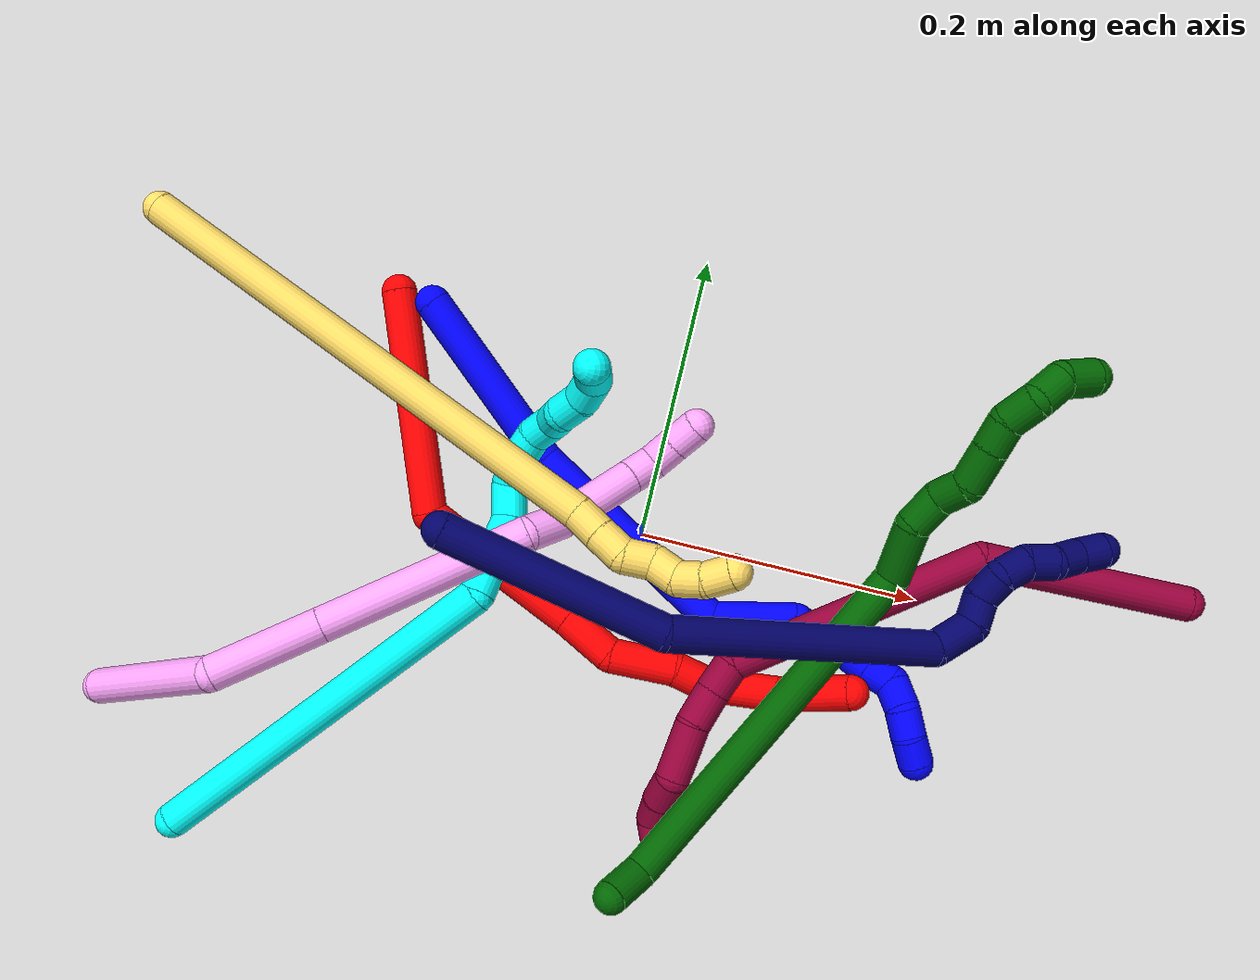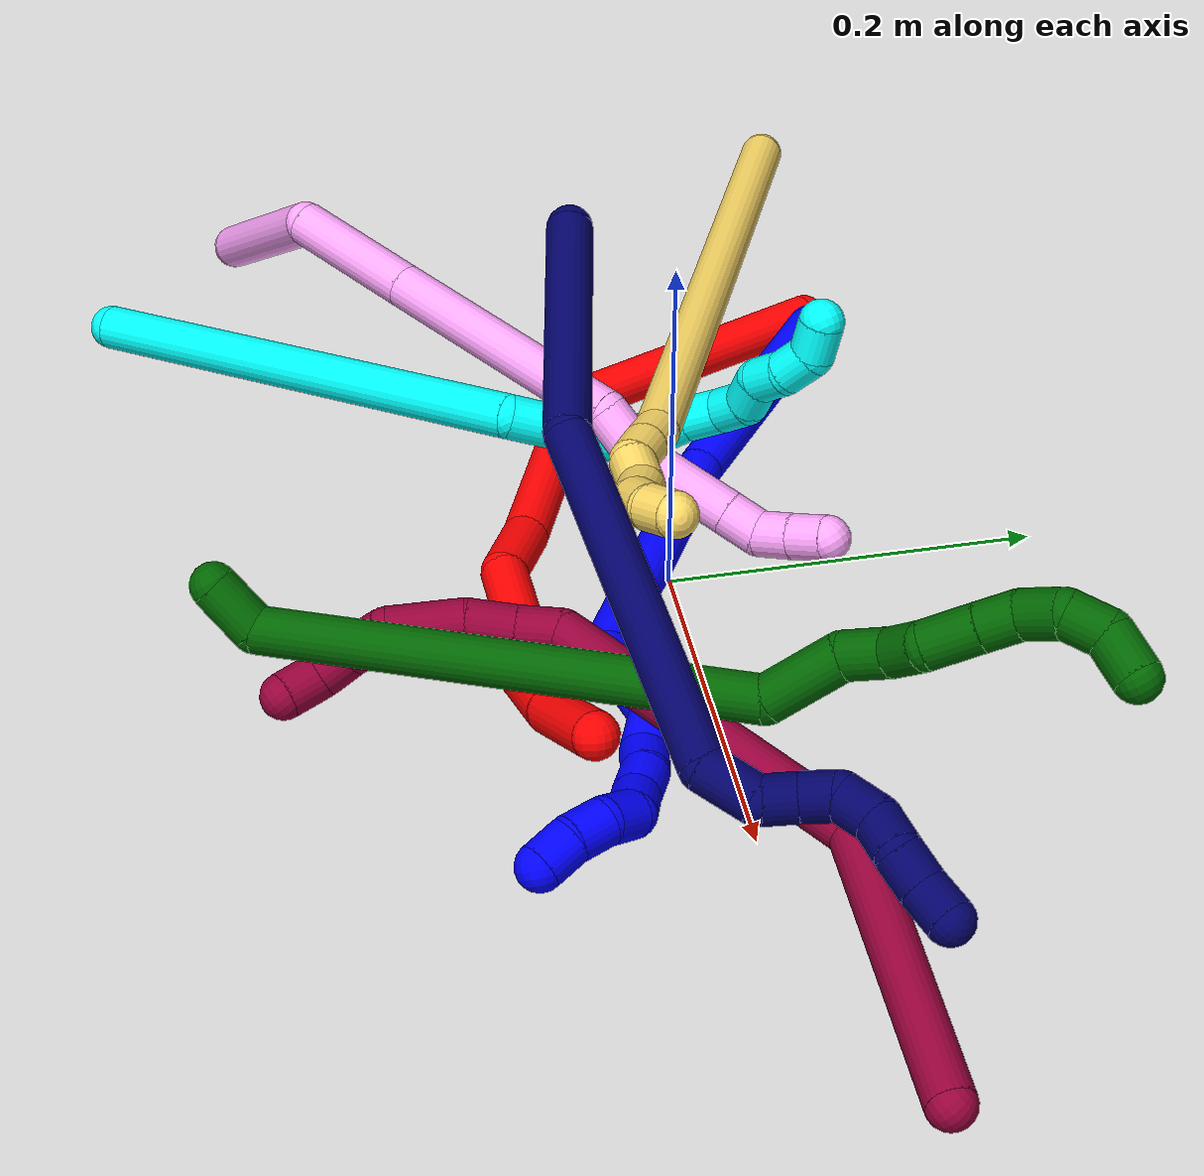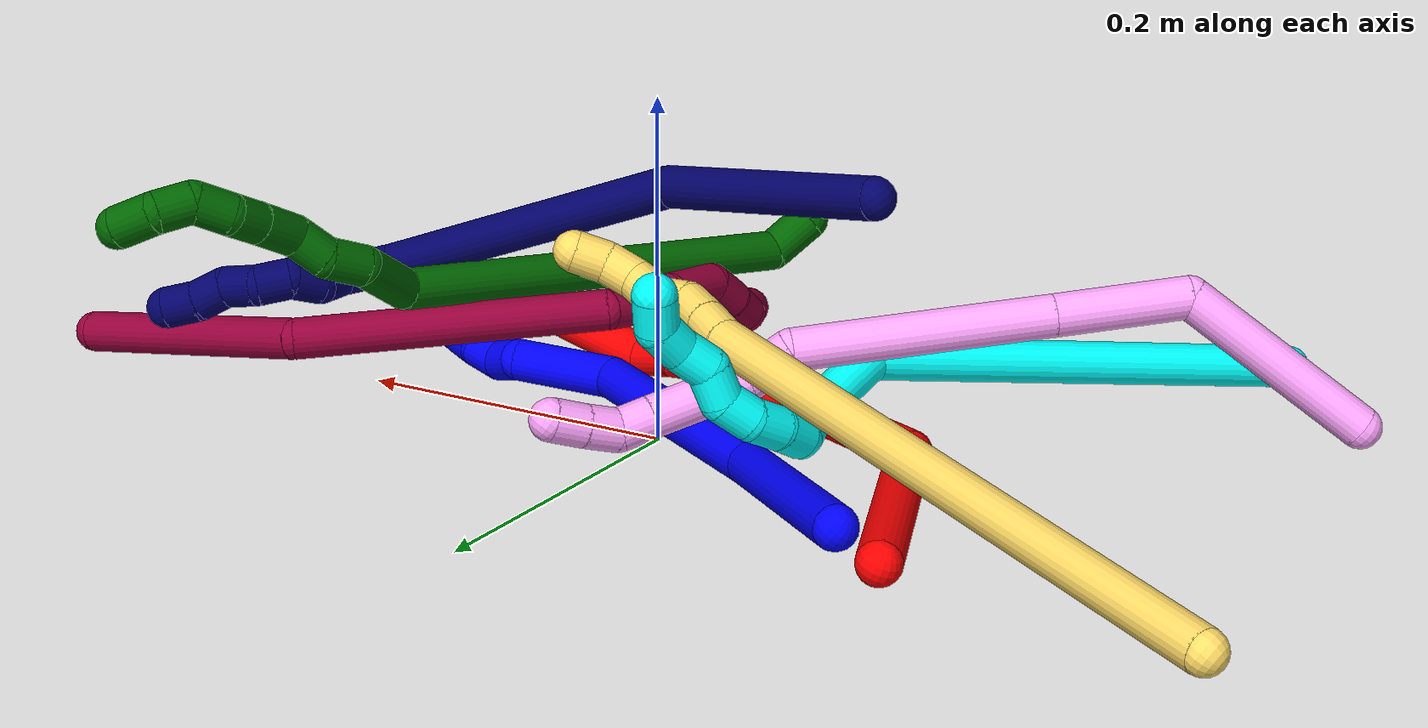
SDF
<sdf version="1.7">
 <world name="default">
  <plugin name="TubeGeneratorPlugin" filename="libtube_generator_plugin.so"/>
  <model name="photoneo_s_sensor">
   <static>1</static>
   <pose>0 0 2 1.57079 1.57079 3.14159</pose>
   <link name="link">
    <inertial><mass>0.1</mass></inertial>
    <sensor name="sensor" type="depth">
     <update_rate>30</update_rate>
     <camera>
      <horizontal_fov>1.22</horizontal_fov>
      <image><width>1920</width><height>1200</height><format>B8G8R8</format></image>
      <clip><near>0.1</near><far>4</far></clip>
      <depth_camera><output>points</output></depth_camera>
     </camera>
     <plugin name="camera_plugin" filename="libgazebo_ros_depth_camera.so">
      <baseline>0.2</baseline>
      <alwaysOn>1</alwaysOn>
      <updateRate>0.0</updateRate>
      <cameraName>camera_ir</cameraName>
      <imageTopicName>/camera/color/image_raw</imageTopicName>
      <cameraInfoTopicName>/camera/color/camera_info</cameraInfoTopicName>
      <depthImageTopicName>/camera/depth/image_raw</depthImageTopicName>
      <depthImageCameraInfoTopicName>/camera/depth/camera_info</depthImageCameraInfoTopicName>
      <pointCloudTopicName>/camera/depth/points</pointCloudTopicName>
      <frameName>fr_optical</frameName>
      <pointCloudCutoff>0.1</pointCloudCutoff>
      <pointCloudCutoffMax>2.0</pointCloudCutoffMax>
      <distortionK1>0</distortionK1>
      <distortionK2>0</distortionK2>
      <distortionK3>0</distortionK3>
      <distortionT1>0</distortionT1>
      <distortionT2>0</distortionT2>
      <CxPrime>0</CxPrime>
      <Cx>0</Cx>
      <Cy>0</Cy>
      <focalLength>0</focalLength>
      <hackBaseline>0</hackBaseline>
     </plugin>
    </sensor>
   </link>
  </model>
  <gravity>0 0 -9.8</gravity>
  <magnetic_field>6e-06 2.3e-05 -4.2e-05</magnetic_field>
  <atmosphere type="adiabatic"/>
  <physics name="default_physics" default="0" type="ode">
   <max_step_size>0.003</max_step_size>
   <real_time_factor>1</real_time_factor>
   <real_time_update_rate>1000</real_time_update_rate>
   <max_contacts>10000</max_contacts>
   <ode>
    <solver>
     <type>quick</type>
     <iters>100</iters>
     <sor>1.3</sor>
     <use_dynamic_moi_rescaling>0</use_dynamic_moi_rescaling>
    </solver>
    <constraints>
     <contact_max_correcting_vel>0</contact_max_correcting_vel>
     <contact_surface_layer>0.001</contact_surface_layer>
     <cfm>0</cfm>
     <erp>0.2</erp>
    </constraints>
   </ode>
  </physics>
  <scene><ambient>0.4 0.4 0.4 1</ambient><background>0.7 0.7 0.7 1</background><shadows>0</shadows></scene>
  <audio><device>default</device></audio>
  <spherical_coordinates>
   <surface_model>EARTH_WGS84</surface_model>
   <latitude_deg>0</latitude_deg>
   <longitude_deg>0</longitude_deg>
   <elevation>0</elevation>
   <heading_deg>0</heading_deg>
  </spherical_coordinates>
  <model name="bin">
   <static>1</static>
   <link name="bottom">
    <collision name="collision-bottom">
     <pose>0 0 -0.01 0 -0 0</pose>
     <geometry><box><size>0.8 0.6 0.02</size></box></geometry>
     <surface>
      <friction><ode><mu>100</mu><mu2>100</mu2></ode></friction>
      <contact><collide_bitmask>65535</collide_bitmask></contact>
     </surface>
    </collision>
   </link>
   <link name="west_wall">
    <collision name="collision-west_wall">
     <pose>-0.41 0 0.1 0 -0 0</pose>
     <geometry><box><size>0.02 0.6 0.2</size></box></geometry>
     <surface>
      <friction><ode><mu>100</mu><mu2>100</mu2></ode></friction>
      <contact><collide_bitmask>65535</collide_bitmask></contact>
     </surface>
    </collision>
   </link>
   <link name="east_wall">
    <collision name="collision-east_wall">
     <pose>0.41 0 0.1 0 -0 0</pose>
     <geometry><box><size>0.02 0.6 0.2</size></box></geometry>
     <surface>
      <friction><ode><mu>100</mu><mu2>100</mu2></ode></friction>
      <contact><collide_bitmask>65535</collide_bitmask></contact>
     </surface>
    </collision>
   </link>
   <link name="south_wall">
    <collision name="collision-south_wall">
     <pose>0 -0.31 0.1 0 -0 0</pose>
     <geometry><box><size>0.8 0.02 0.2</size></box></geometry>
     <surface>
      <friction><ode><mu>100</mu><mu2>100</mu2></ode></friction>
      <contact><collide_bitmask>65535</collide_bitmask></contact>
     </surface>
    </collision>
   </link>
   <link name="north_wall">
    <collision name="collision-north_wall">
     <pose>0 0.31 0.1 0 -0 0</pose>
     <geometry><box><size>0.8 0.02 0.2</size></box></geometry>
     <surface>
      <friction><ode><mu>100</mu><mu2>100</mu2></ode></friction>
      <contact><collide_bitmask>65535</collide_bitmask></contact>
     </surface>
    </collision>
   </link>
  </model>
  <model name="1">
   <static>0</static>
   <link name="1">
    <collision name="collision-cylinder-e_1_1_4">
     <pose>0.017856 -0.05655 -0.031979 2.08546 0.268232 0.454618</pose>
     <geometry><cylinder><radius>0.0125</radius><length>0.13475</length></cylinder></geometry>
     <surface>
      <friction><ode><mu>1.16</mu><mu2>1.16</mu2><slip1>0</slip1><slip2>0</slip2></ode></friction>
      <contact><ode><kp>1e+06</kp><kd>1</kd><max_vel>0</max_vel><min_depth>0.001</min_depth></ode></contact>
     </surface>
    </collision>
    <visual name="visual-cylinder-e_1_1_4">
     <pose>0.017856 -0.05655 -0.031979 2.08546 0.268232 0.454618</pose>
     <geometry><cylinder><radius>0.0125</radius><length>0.13475</length></cylinder></geometry>
     <material><ambient>0 0 1 1</ambient></material>
    </visual>
    <collision name="collision-cylinder-e_2_4_5">
     <pose>0.073114 -0.174433 -0.102809 2.13545 0.475695 0.82994</pose>
     <geometry><cylinder><radius>0.0125</radius><length>0.163341</length></cylinder></geometry>
     <surface>
      <friction><ode><mu>1.16</mu><mu2>1.16</mu2><slip1>0</slip1><slip2>0</slip2></ode></friction>
      <contact><ode><kp>1e+06</kp><kd>1</kd><max_vel>0</max_vel><min_depth>0.001</min_depth></ode></contact>
     </surface>
    </collision>
    <visual name="visual-cylinder-e_2_4_5">
     <pose>0.073114 -0.174433 -0.102809 2.13545 0.475695 0.82994</pose>
     <geometry><cylinder><radius>0.0125</radius><length>0.163341</length></cylinder></geometry>
     <material><ambient>0 0 1 1</ambient></material>
    </visual>
    <collision name="collision-cylinder-e_3_5_6">
     <pose>0.13516 -0.239554 -0.158117 2.91536 0.970055 2.71698</pose>
     <geometry><cylinder><radius>0.0125</radius><length>0.059751</length></cylinder></geometry>
     <surface>
      <friction><ode><mu>1.16</mu><mu2>1.16</mu2><slip1>0</slip1><slip2>0</slip2></ode></friction>
      <contact><ode><kp>1e+06</kp><kd>1</kd><max_vel>0</max_vel><min_depth>0.001</min_depth></ode></contact>
     </surface>
    </collision>
    <visual name="visual-cylinder-e_3_5_6">
     <pose>0.13516 -0.239554 -0.158117 2.91536 0.970055 2.71698</pose>
     <geometry><cylinder><radius>0.0125</radius><length>0.059751</length></cylinder></geometry>
     <material><ambient>0 0 1 1</ambient></material>
    </visual>
    <collision name="collision-cylinder-e_4_6_7">
     <pose>0.163376 -0.250177 -0.182399 2.42365 0.331082 0.837793</pose>
     <geometry><cylinder><radius>0.0125</radius><length>0.021972</length></cylinder></geometry>
     <surface>
      <friction><ode><mu>1.16</mu><mu2>1.16</mu2><slip1>0</slip1><slip2>0</slip2></ode></friction>
      <contact><ode><kp>1e+06</kp><kd>1</kd><max_vel>0</max_vel><min_depth>0.001</min_depth></ode></contact>
     </surface>
    </collision>
    <visual name="visual-cylinder-e_4_6_7">
     <pose>0.163376 -0.250177 -0.182399 2.42365 0.331082 0.837793</pose>
     <geometry><cylinder><radius>0.0125</radius><length>0.021972</length></cylinder></geometry>
     <material><ambient>0 0 1 1</ambient></material>
    </visual>
    <collision name="collision-cylinder-e_5_7_8">
     <pose>0.174623 -0.262072 -0.194185 2.23492 0.873708 1.52839</pose>
     <geometry><cylinder><radius>0.0125</radius><length>0.020023</length></cylinder></geometry>
     <surface>
      <friction><ode><mu>1.16</mu><mu2>1.16</mu2><slip1>0</slip1><slip2>0</slip2></ode></friction>
      <contact><ode><kp>1e+06</kp><kd>1</kd><max_vel>0</max_vel><min_depth>0.001</min_depth></ode></contact>
     </surface>
    </collision>
    <visual name="visual-cylinder-e_5_7_8">
     <pose>0.174623 -0.262072 -0.194185 2.23492 0.873708 1.52839</pose>
     <geometry><cylinder><radius>0.0125</radius><length>0.020023</length></cylinder></geometry>
     <material><ambient>0 0 1 1</ambient></material>
    </visual>
    <collision name="collision-cylinder-e_6_8_9">
     <pose>0.188172 -0.274199 -0.202269 2.09893 0.622681 1.02146</pose>
     <geometry><cylinder><radius>0.0125</radius><length>0.020141</length></cylinder></geometry>
     <surface>
      <friction><ode><mu>1.16</mu><mu2>1.16</mu2><slip1>0</slip1><slip2>0</slip2></ode></friction>
      <contact><ode><kp>1e+06</kp><kd>1</kd><max_vel>0</max_vel><min_depth>0.001</min_depth></ode></contact>
     </surface>
    </collision>
    <visual name="visual-cylinder-e_6_8_9">
     <pose>0.188172 -0.274199 -0.202269 2.09893 0.622681 1.02146</pose>
     <geometry><cylinder><radius>0.0125</radius><length>0.020141</length></cylinder></geometry>
     <material><ambient>0 0 1 1</ambient></material>
    </visual>
    <collision name="collision-cylinder-e_7_9_10">
     <pose>0.201448 -0.287356 -0.209251 2.00972 0.833036 1.21664</pose>
     <geometry><cylinder><radius>0.0125</radius><length>0.020008</length></cylinder></geometry>
     <surface>
      <friction><ode><mu>1.16</mu><mu2>1.16</mu2><slip1>0</slip1><slip2>0</slip2></ode></friction>
      <contact><ode><kp>1e+06</kp><kd>1</kd><max_vel>0</max_vel><min_depth>0.001</min_depth></ode></contact>
     </surface>
    </collision>
    <visual name="visual-cylinder-e_7_9_10">
     <pose>0.201448 -0.287356 -0.209251 2.00972 0.833036 1.21664</pose>
     <geometry><cylinder><radius>0.0125</radius><length>0.020008</length></cylinder></geometry>
     <material><ambient>0 0 1 1</ambient></material>
    </visual>
    <collision name="collision-cylinder-e_8_10_11">
     <pose>0.212036 -0.302907 -0.211479 1.50411 0.324139 0.303544</pose>
     <geometry><cylinder><radius>0.0125</radius><length>0.020005</length></cylinder></geometry>
     <surface>
      <friction><ode><mu>1.16</mu><mu2>1.16</mu2><slip1>0</slip1><slip2>0</slip2></ode></friction>
      <contact><ode><kp>1e+06</kp><kd>1</kd><max_vel>0</max_vel><min_depth>0.001</min_depth></ode></contact>
     </surface>
    </collision>
    <visual name="visual-cylinder-e_8_10_11">
     <pose>0.212036 -0.302907 -0.211479 1.50411 0.324139 0.303544</pose>
     <geometry><cylinder><radius>0.0125</radius><length>0.020005</length></cylinder></geometry>
     <material><ambient>0 0 1 1</ambient></material>
    </visual>
    <collision name="collision-cylinder-e_9_11_12">
     <pose>0.215313 -0.322177 -0.212798 1.76709 0.00915 0.011149</pose>
     <geometry><cylinder><radius>0.0125</radius><length>0.020005</length></cylinder></geometry>
     <surface>
      <friction><ode><mu>1.16</mu><mu2>1.16</mu2><slip1>0</slip1><slip2>0</slip2></ode></friction>
      <contact><ode><kp>1e+06</kp><kd>1</kd><max_vel>0</max_vel><min_depth>0.001</min_depth></ode></contact>
     </surface>
    </collision>
    <visual name="visual-cylinder-e_9_11_12">
     <pose>0.215313 -0.322177 -0.212798 1.76709 0.00915 0.011149</pose>
     <geometry><cylinder><radius>0.0125</radius><length>0.020005</length></cylinder></geometry>
     <material><ambient>0 0 1 1</ambient></material>
    </visual>
    <collision name="collision-cylinder-e_10_12_2">
     <pose>0.21461 -0.341018 -0.218977 2.00871 -0.079585 -0.125044</pose>
     <geometry><cylinder><radius>0.0125</radius><length>0.020006</length></cylinder></geometry>
     <surface>
      <friction><ode><mu>1.16</mu><mu2>1.16</mu2><slip1>0</slip1><slip2>0</slip2></ode></friction>
      <contact><ode><kp>1e+06</kp><kd>1</kd><max_vel>0</max_vel><min_depth>0.001</min_depth></ode></contact>
     </surface>
    </collision>
    <visual name="visual-cylinder-e_10_12_2">
     <pose>0.21461 -0.341018 -0.218977 2.00871 -0.079585 -0.125044</pose>
     <geometry><cylinder><radius>0.0125</radius><length>0.020006</length></cylinder></geometry>
     <material><ambient>0 0 1 1</ambient></material>
    </visual>
    <collision name="collision-sphere-2">
     <pose>0.213814 -0.350048 -0.223205 0 -0 0</pose>
     <geometry><sphere><radius>0.0125</radius></sphere></geometry>
     <surface>
      <friction><ode><mu>1.16</mu><mu2>1.16</mu2><slip1>0</slip1><slip2>0</slip2></ode></friction>
      <contact><ode><kp>1e+06</kp><kd>1</kd><max_vel>0</max_vel><min_depth>0.001</min_depth></ode></contact>
     </surface>
    </collision>
    <visual name="visual-sphere-2">
     <pose>0.213814 -0.350048 -0.223205 0 -0 0</pose>
     <geometry><sphere><radius>0.0125</radius></sphere></geometry>
     <material><ambient>0 0 1 1</ambient></material>
    </visual>
    <collision name="collision-sphere-12">
     <pose>0.215405 -0.331987 -0.214748 0 -0 0</pose>
     <geometry><sphere><radius>0.0125</radius></sphere></geometry>
     <surface>
      <friction><ode><mu>1.16</mu><mu2>1.16</mu2><slip1>0</slip1><slip2>0</slip2></ode></friction>
      <contact><ode><kp>1e+06</kp><kd>1</kd><max_vel>0</max_vel><min_depth>0.001</min_depth></ode></contact>
     </surface>
    </collision>
    <visual name="visual-sphere-12">
     <pose>0.215405 -0.331987 -0.214748 0 -0 0</pose>
     <geometry><sphere><radius>0.0125</radius></sphere></geometry>
     <material><ambient>0 0 1 1</ambient></material>
    </visual>
    <collision name="collision-sphere-11">
     <pose>0.215222 -0.312368 -0.210847 0 -0 0</pose>
     <geometry><sphere><radius>0.0125</radius></sphere></geometry>
     <surface>
      <friction><ode><mu>1.16</mu><mu2>1.16</mu2><slip1>0</slip1><slip2>0</slip2></ode></friction>
      <contact><ode><kp>1e+06</kp><kd>1</kd><max_vel>0</max_vel><min_depth>0.001</min_depth></ode></contact>
     </surface>
    </collision>
    <visual name="visual-sphere-11">
     <pose>0.215222 -0.312368 -0.210847 0 -0 0</pose>
     <geometry><sphere><radius>0.0125</radius></sphere></geometry>
     <material><ambient>0 0 1 1</ambient></material>
    </visual>
    <collision name="collision-sphere-10">
     <pose>0.20885 -0.293447 -0.212111 0 -0 0</pose>
     <geometry><sphere><radius>0.0125</radius></sphere></geometry>
     <surface>
      <friction><ode><mu>1.16</mu><mu2>1.16</mu2><slip1>0</slip1><slip2>0</slip2></ode></friction>
      <contact><ode><kp>1e+06</kp><kd>1</kd><max_vel>0</max_vel><min_depth>0.001</min_depth></ode></contact>
     </surface>
    </collision>
    <visual name="visual-sphere-10">
     <pose>0.20885 -0.293447 -0.212111 0 -0 0</pose>
     <geometry><sphere><radius>0.0125</radius></sphere></geometry>
     <material><ambient>0 0 1 1</ambient></material>
    </visual>
    <collision name="collision-sphere-9">
     <pose>0.194045 -0.281265 -0.206391 0 -0 0</pose>
     <geometry><sphere><radius>0.0125</radius></sphere></geometry>
     <surface>
      <friction><ode><mu>1.16</mu><mu2>1.16</mu2><slip1>0</slip1><slip2>0</slip2></ode></friction>
      <contact><ode><kp>1e+06</kp><kd>1</kd><max_vel>0</max_vel><min_depth>0.001</min_depth></ode></contact>
     </surface>
    </collision>
    <visual name="visual-sphere-9">
     <pose>0.194045 -0.281265 -0.206391 0 -0 0</pose>
     <geometry><sphere><radius>0.0125</radius></sphere></geometry>
     <material><ambient>0 0 1 1</ambient></material>
    </visual>
    <collision name="collision-sphere-4">
     <pose>0.035712 -0.1131 -0.063958 0 -0 0</pose>
     <geometry><sphere><radius>0.0125</radius></sphere></geometry>
     <surface>
      <friction><ode><mu>1.16</mu><mu2>1.16</mu2><slip1>0</slip1><slip2>0</slip2></ode></friction>
      <contact><ode><kp>1e+06</kp><kd>1</kd><max_vel>0</max_vel><min_depth>0.001</min_depth></ode></contact>
     </surface>
    </collision>
    <visual name="visual-sphere-4">
     <pose>0.035712 -0.1131 -0.063958 0 -0 0</pose>
     <geometry><sphere><radius>0.0125</radius></sphere></geometry>
     <material><ambient>0 0 1 1</ambient></material>
    </visual>
    <collision name="collision-sphere-1">
     <geometry><sphere><radius>0.0125</radius></sphere></geometry>
     <surface>
      <friction><ode><mu>1.16</mu><mu2>1.16</mu2><slip1>0</slip1><slip2>0</slip2></ode></friction>
      <contact><ode><kp>1e+06</kp><kd>1</kd><max_vel>0</max_vel><min_depth>0.001</min_depth></ode></contact>
     </surface>
    </collision>
    <visual name="visual-sphere-1">
     <geometry><sphere><radius>0.0125</radius></sphere></geometry>
     <material><ambient>0 0 1 1</ambient></material>
    </visual>
    <collision name="collision-sphere-8">
     <pose>0.182299 -0.267133 -0.198147 0 -0 0</pose>
     <geometry><sphere><radius>0.0125</radius></sphere></geometry>
     <surface>
      <friction><ode><mu>1.16</mu><mu2>1.16</mu2><slip1>0</slip1><slip2>0</slip2></ode></friction>
      <contact><ode><kp>1e+06</kp><kd>1</kd><max_vel>0</max_vel><min_depth>0.001</min_depth></ode></contact>
     </surface>
    </collision>
    <visual name="visual-sphere-8">
     <pose>0.182299 -0.267133 -0.198147 0 -0 0</pose>
     <geometry><sphere><radius>0.0125</radius></sphere></geometry>
     <material><ambient>0 0 1 1</ambient></material>
    </visual>
    <collision name="collision-sphere-5">
     <pose>0.110515 -0.235766 -0.141661 0 -0 0</pose>
     <geometry><sphere><radius>0.0125</radius></sphere></geometry>
     <surface>
      <friction><ode><mu>1.16</mu><mu2>1.16</mu2><slip1>0</slip1><slip2>0</slip2></ode></friction>
      <contact><ode><kp>1e+06</kp><kd>1</kd><max_vel>0</max_vel><min_depth>0.001</min_depth></ode></contact>
     </surface>
    </collision>
    <visual name="visual-sphere-5">
     <pose>0.110515 -0.235766 -0.141661 0 -0 0</pose>
     <geometry><sphere><radius>0.0125</radius></sphere></geometry>
     <material><ambient>0 0 1 1</ambient></material>
    </visual>
    <collision name="collision-sphere-6">
     <pose>0.159805 -0.243342 -0.174574 0 -0 0</pose>
     <geometry><sphere><radius>0.0125</radius></sphere></geometry>
     <surface>
      <friction><ode><mu>1.16</mu><mu2>1.16</mu2><slip1>0</slip1><slip2>0</slip2></ode></friction>
      <contact><ode><kp>1e+06</kp><kd>1</kd><max_vel>0</max_vel><min_depth>0.001</min_depth></ode></contact>
     </surface>
    </collision>
    <visual name="visual-sphere-6">
     <pose>0.159805 -0.243342 -0.174574 0 -0 0</pose>
     <geometry><sphere><radius>0.0125</radius></sphere></geometry>
     <material><ambient>0 0 1 1</ambient></material>
    </visual>
    <collision name="collision-sphere-7">
     <pose>0.166947 -0.257011 -0.190224 0 -0 0</pose>
     <geometry><sphere><radius>0.0125</radius></sphere></geometry>
     <surface>
      <friction><ode><mu>1.16</mu><mu2>1.16</mu2><slip1>0</slip1><slip2>0</slip2></ode></friction>
      <contact><ode><kp>1e+06</kp><kd>1</kd><max_vel>0</max_vel><min_depth>0.001</min_depth></ode></contact>
     </surface>
    </collision>
    <visual name="visual-sphere-7">
     <pose>0.166947 -0.257011 -0.190224 0 -0 0</pose>
     <geometry><sphere><radius>0.0125</radius></sphere></geometry>
     <material><ambient>0 0 1 1</ambient></material>
    </visual>
    <inertial>
     <pose>0.100347 -0.183538 -0.119149 0 -0 0</pose>
     <mass>0.5</mass>
     <inertia>
      <ixx>0.000756</ixx>
      <ixy>0</ixy>
      <ixz>0</ixz>
      <iyy>0.000233</iyy>
      <iyz>0</iyz>
      <izz>0.000201</izz>
     </inertia>
    </inertial>
   </link>
   <pose>-0.181035 0.122595 0.02462 -0.175952 -0.645982 0.440877</pose>
  </model>
  <model name="2">
   <static>0</static>
   <link name="2">
    <collision name="collision-cylinder-e_1_1_4">
     <pose>-0.015448 -0.078091 -0.00939 1.69047 -0.193933 -0.218465</pose>
     <geometry><cylinder><radius>0.0125</radius><length>0.160313</length></cylinder></geometry>
     <surface>
      <friction><ode><mu>1.16</mu><mu2>1.16</mu2><slip1>0</slip1><slip2>0</slip2></ode></friction>
      <contact><ode><kp>1e+06</kp><kd>1</kd><max_vel>0</max_vel><min_depth>0.001</min_depth></ode></contact>
     </surface>
    </collision>
    <visual name="visual-cylinder-e_1_1_4">
     <pose>-0.015448 -0.078091 -0.00939 1.69047 -0.193933 -0.218465</pose>
     <geometry><cylinder><radius>0.0125</radius><length>0.160313</length></cylinder></geometry>
     <material><ambient>1 0 0 1</ambient></material>
    </visual>
    <collision name="collision-cylinder-e_2_4_5">
     <pose>0.000147 -0.204041 -0.040626 1.99901 0.533081 0.803347</pose>
     <geometry><cylinder><radius>0.0125</radius><length>0.122167</length></cylinder></geometry>
     <surface>
      <friction><ode><mu>1.16</mu><mu2>1.16</mu2><slip1>0</slip1><slip2>0</slip2></ode></friction>
      <contact><ode><kp>1e+06</kp><kd>1</kd><max_vel>0</max_vel><min_depth>0.001</min_depth></ode></contact>
     </surface>
    </collision>
    <visual name="visual-cylinder-e_2_4_5">
     <pose>0.000147 -0.204041 -0.040626 1.99901 0.533081 0.803347</pose>
     <geometry><cylinder><radius>0.0125</radius><length>0.122167</length></cylinder></geometry>
     <material><ambient>1 0 0 1</ambient></material>
    </visual>
    <collision name="collision-cylinder-e_3_5_6">
     <pose>0.04147 -0.268663 -0.066607 1.81266 0.537029 0.675647</pose>
     <geometry><cylinder><radius>0.0125</radius><length>0.040193</length></cylinder></geometry>
     <surface>
      <friction><ode><mu>1.16</mu><mu2>1.16</mu2><slip1>0</slip1><slip2>0</slip2></ode></friction>
      <contact><ode><kp>1e+06</kp><kd>1</kd><max_vel>0</max_vel><min_depth>0.001</min_depth></ode></contact>
     </surface>
    </collision>
    <visual name="visual-cylinder-e_3_5_6">
     <pose>0.04147 -0.268663 -0.066607 1.81266 0.537029 0.675647</pose>
     <geometry><cylinder><radius>0.0125</radius><length>0.040193</length></cylinder></geometry>
     <material><ambient>1 0 0 1</ambient></material>
    </visual>
    <collision name="collision-cylinder-e_4_6_7">
     <pose>0.069839 -0.295875 -0.08074 2.33418 0.896418 1.68889</pose>
     <geometry><cylinder><radius>0.0125</radius><length>0.046314</length></cylinder></geometry>
     <surface>
      <friction><ode><mu>1.16</mu><mu2>1.16</mu2><slip1>0</slip1><slip2>0</slip2></ode></friction>
      <contact><ode><kp>1e+06</kp><kd>1</kd><max_vel>0</max_vel><min_depth>0.001</min_depth></ode></contact>
     </surface>
    </collision>
    <visual name="visual-cylinder-e_4_6_7">
     <pose>0.069839 -0.295875 -0.08074 2.33418 0.896418 1.68889</pose>
     <geometry><cylinder><radius>0.0125</radius><length>0.046314</length></cylinder></geometry>
     <material><ambient>1 0 0 1</ambient></material>
    </visual>
    <collision name="collision-cylinder-e_5_7_8">
     <pose>0.095507 -0.314374 -0.098064 2.30909 0.608229 1.23473</pose>
     <geometry><cylinder><radius>0.0125</radius><length>0.026531</length></cylinder></geometry>
     <surface>
      <friction><ode><mu>1.16</mu><mu2>1.16</mu2><slip1>0</slip1><slip2>0</slip2></ode></friction>
      <contact><ode><kp>1e+06</kp><kd>1</kd><max_vel>0</max_vel><min_depth>0.001</min_depth></ode></contact>
     </surface>
    </collision>
    <visual name="visual-cylinder-e_5_7_8">
     <pose>0.095507 -0.314374 -0.098064 2.30909 0.608229 1.23473</pose>
     <geometry><cylinder><radius>0.0125</radius><length>0.026531</length></cylinder></geometry>
     <material><ambient>1 0 0 1</ambient></material>
    </visual>
    <collision name="collision-cylinder-e_6_8_9">
     <pose>0.127082 -0.333381 -0.10751 1.7619 1.13553 1.31617</pose>
     <geometry><cylinder><radius>0.0125</radius><length>0.052926</length></cylinder></geometry>
     <surface>
      <friction><ode><mu>1.16</mu><mu2>1.16</mu2><slip1>0</slip1><slip2>0</slip2></ode></friction>
      <contact><ode><kp>1e+06</kp><kd>1</kd><max_vel>0</max_vel><min_depth>0.001</min_depth></ode></contact>
     </surface>
    </collision>
    <visual name="visual-cylinder-e_6_8_9">
     <pose>0.127082 -0.333381 -0.10751 1.7619 1.13553 1.31617</pose>
     <geometry><cylinder><radius>0.0125</radius><length>0.052926</length></cylinder></geometry>
     <material><ambient>1 0 0 1</ambient></material>
    </visual>
    <collision name="collision-cylinder-e_7_9_2">
     <pose>0.17588 -0.35132 -0.108874 1.46307 1.29482 1.19267</pose>
     <geometry><cylinder><radius>0.0125</radius><length>0.051555</length></cylinder></geometry>
     <surface>
      <friction><ode><mu>1.16</mu><mu2>1.16</mu2><slip1>0</slip1><slip2>0</slip2></ode></friction>
      <contact><ode><kp>1e+06</kp><kd>1</kd><max_vel>0</max_vel><min_depth>0.001</min_depth></ode></contact>
     </surface>
    </collision>
    <visual name="visual-cylinder-e_7_9_2">
     <pose>0.17588 -0.35132 -0.108874 1.46307 1.29482 1.19267</pose>
     <geometry><cylinder><radius>0.0125</radius><length>0.051555</length></cylinder></geometry>
     <material><ambient>1 0 0 1</ambient></material>
    </visual>
    <collision name="collision-sphere-2">
     <pose>0.200683 -0.358303 -0.108119 0 -0 0</pose>
     <geometry><sphere><radius>0.0125</radius></sphere></geometry>
     <surface>
      <friction><ode><mu>1.16</mu><mu2>1.16</mu2><slip1>0</slip1><slip2>0</slip2></ode></friction>
      <contact><ode><kp>1e+06</kp><kd>1</kd><max_vel>0</max_vel><min_depth>0.001</min_depth></ode></contact>
     </surface>
    </collision>
    <visual name="visual-sphere-2">
     <pose>0.200683 -0.358303 -0.108119 0 -0 0</pose>
     <geometry><sphere><radius>0.0125</radius></sphere></geometry>
     <material><ambient>1 0 0 1</ambient></material>
    </visual>
    <collision name="collision-sphere-9">
     <pose>0.151078 -0.344336 -0.109629 0 -0 0</pose>
     <geometry><sphere><radius>0.0125</radius></sphere></geometry>
     <surface>
      <friction><ode><mu>1.16</mu><mu2>1.16</mu2><slip1>0</slip1><slip2>0</slip2></ode></friction>
      <contact><ode><kp>1e+06</kp><kd>1</kd><max_vel>0</max_vel><min_depth>0.001</min_depth></ode></contact>
     </surface>
    </collision>
    <visual name="visual-sphere-9">
     <pose>0.151078 -0.344336 -0.109629 0 -0 0</pose>
     <geometry><sphere><radius>0.0125</radius></sphere></geometry>
     <material><ambient>1 0 0 1</ambient></material>
    </visual>
    <collision name="collision-sphere-4">
     <pose>-0.030895 -0.156183 -0.018781 0 -0 0</pose>
     <geometry><sphere><radius>0.0125</radius></sphere></geometry>
     <surface>
      <friction><ode><mu>1.16</mu><mu2>1.16</mu2><slip1>0</slip1><slip2>0</slip2></ode></friction>
      <contact><ode><kp>1e+06</kp><kd>1</kd><max_vel>0</max_vel><min_depth>0.001</min_depth></ode></contact>
     </surface>
    </collision>
    <visual name="visual-sphere-4">
     <pose>-0.030895 -0.156183 -0.018781 0 -0 0</pose>
     <geometry><sphere><radius>0.0125</radius></sphere></geometry>
     <material><ambient>1 0 0 1</ambient></material>
    </visual>
    <collision name="collision-sphere-1">
     <geometry><sphere><radius>0.0125</radius></sphere></geometry>
     <surface>
      <friction><ode><mu>1.16</mu><mu2>1.16</mu2><slip1>0</slip1><slip2>0</slip2></ode></friction>
      <contact><ode><kp>1e+06</kp><kd>1</kd><max_vel>0</max_vel><min_depth>0.001</min_depth></ode></contact>
     </surface>
    </collision>
    <visual name="visual-sphere-1">
     <geometry><sphere><radius>0.0125</radius></sphere></geometry>
     <material><ambient>1 0 0 1</ambient></material>
    </visual>
    <collision name="collision-sphere-8">
     <pose>0.103087 -0.322426 -0.105391 0 -0 0</pose>
     <geometry><sphere><radius>0.0125</radius></sphere></geometry>
     <surface>
      <friction><ode><mu>1.16</mu><mu2>1.16</mu2><slip1>0</slip1><slip2>0</slip2></ode></friction>
      <contact><ode><kp>1e+06</kp><kd>1</kd><max_vel>0</max_vel><min_depth>0.001</min_depth></ode></contact>
     </surface>
    </collision>
    <visual name="visual-sphere-8">
     <pose>0.103087 -0.322426 -0.105391 0 -0 0</pose>
     <geometry><sphere><radius>0.0125</radius></sphere></geometry>
     <material><ambient>1 0 0 1</ambient></material>
    </visual>
    <collision name="collision-sphere-5">
     <pose>0.031189 -0.251898 -0.062471 0 -0 0</pose>
     <geometry><sphere><radius>0.0125</radius></sphere></geometry>
     <surface>
      <friction><ode><mu>1.16</mu><mu2>1.16</mu2><slip1>0</slip1><slip2>0</slip2></ode></friction>
      <contact><ode><kp>1e+06</kp><kd>1</kd><max_vel>0</max_vel><min_depth>0.001</min_depth></ode></contact>
     </surface>
    </collision>
    <visual name="visual-sphere-5">
     <pose>0.031189 -0.251898 -0.062471 0 -0 0</pose>
     <geometry><sphere><radius>0.0125</radius></sphere></geometry>
     <material><ambient>1 0 0 1</ambient></material>
    </visual>
    <collision name="collision-sphere-6">
     <pose>0.051751 -0.285428 -0.070743 0 -0 0</pose>
     <geometry><sphere><radius>0.0125</radius></sphere></geometry>
     <surface>
      <friction><ode><mu>1.16</mu><mu2>1.16</mu2><slip1>0</slip1><slip2>0</slip2></ode></friction>
      <contact><ode><kp>1e+06</kp><kd>1</kd><max_vel>0</max_vel><min_depth>0.001</min_depth></ode></contact>
     </surface>
    </collision>
    <visual name="visual-sphere-6">
     <pose>0.051751 -0.285428 -0.070743 0 -0 0</pose>
     <geometry><sphere><radius>0.0125</radius></sphere></geometry>
     <material><ambient>1 0 0 1</ambient></material>
    </visual>
    <collision name="collision-sphere-7">
     <pose>0.087926 -0.306322 -0.090737 0 -0 0</pose>
     <geometry><sphere><radius>0.0125</radius></sphere></geometry>
     <surface>
      <friction><ode><mu>1.16</mu><mu2>1.16</mu2><slip1>0</slip1><slip2>0</slip2></ode></friction>
      <contact><ode><kp>1e+06</kp><kd>1</kd><max_vel>0</max_vel><min_depth>0.001</min_depth></ode></contact>
     </surface>
    </collision>
    <visual name="visual-sphere-7">
     <pose>0.087926 -0.306322 -0.090737 0 -0 0</pose>
     <geometry><sphere><radius>0.0125</radius></sphere></geometry>
     <material><ambient>1 0 0 1</ambient></material>
    </visual>
    <inertial>
     <pose>0.04154 -0.212091 -0.05358 0 -0 0</pose>
     <mass>0.5</mass>
     <inertia>
      <ixx>0.000496</ixx>
      <ixy>0</ixy>
      <ixz>0</ixz>
      <iyy>2.9e-05</iyy>
      <iyz>0</iyz>
      <izz>0.000425</izz>
     </inertia>
    </inertial>
   </link>
   <pose>-0.20831 0.12639 0.012426 -0.200738 -0.358597 0.587156</pose>
  </model>
  <model name="3">
   <static>0</static>
   <link name="3">
    <collision name="collision-cylinder-e_1_1_4">
     <pose>0.072057 0.089843 -0.072502 -2.24978 0.557988 -1.07978</pose>
     <geometry><cylinder><radius>0.0125</radius><length>0.272179</length></cylinder></geometry>
     <surface>
      <friction><ode><mu>1.16</mu><mu2>1.16</mu2><slip1>0</slip1><slip2>0</slip2></ode></friction>
      <contact><ode><kp>1e+06</kp><kd>1</kd><max_vel>0</max_vel><min_depth>0.001</min_depth></ode></contact>
     </surface>
    </collision>
    <visual name="visual-cylinder-e_1_1_4">
     <pose>0.072057 0.089843 -0.072502 -2.24978 0.557988 -1.07978</pose>
     <geometry><cylinder><radius>0.0125</radius><length>0.272179</length></cylinder></geometry>
     <material><ambient>0.003922 1 0.996078 1</ambient></material>
    </visual>
    <collision name="collision-cylinder-e_2_4_5">
     <pose>0.139743 0.203593 -0.161823 -2.18387 -0.148409 0.284452</pose>
     <geometry><cylinder><radius>0.0125</radius><length>0.059112</length></cylinder></geometry>
     <surface>
      <friction><ode><mu>1.16</mu><mu2>1.16</mu2><slip1>0</slip1><slip2>0</slip2></ode></friction>
      <contact><ode><kp>1e+06</kp><kd>1</kd><max_vel>0</max_vel><min_depth>0.001</min_depth></ode></contact>
     </surface>
    </collision>
    <visual name="visual-cylinder-e_2_4_5">
     <pose>0.139743 0.203593 -0.161823 -2.18387 -0.148409 0.284452</pose>
     <geometry><cylinder><radius>0.0125</radius><length>0.059112</length></cylinder></geometry>
     <material><ambient>0.003922 1 0.996078 1</ambient></material>
    </visual>
    <collision name="collision-cylinder-e_3_5_6">
     <pose>0.130841 0.239225 -0.181825 -1.83591 -0.357025 0.463431</pose>
     <geometry><cylinder><radius>0.0125</radius><length>0.025934</length></cylinder></geometry>
     <surface>
      <friction><ode><mu>1.16</mu><mu2>1.16</mu2><slip1>0</slip1><slip2>0</slip2></ode></friction>
      <contact><ode><kp>1e+06</kp><kd>1</kd><max_vel>0</max_vel><min_depth>0.001</min_depth></ode></contact>
     </surface>
    </collision>
    <visual name="visual-cylinder-e_3_5_6">
     <pose>0.130841 0.239225 -0.181825 -1.83591 -0.357025 0.463431</pose>
     <geometry><cylinder><radius>0.0125</radius><length>0.025934</length></cylinder></geometry>
     <material><ambient>0.003922 1 0.996078 1</ambient></material>
    </visual>
    <collision name="collision-cylinder-e_4_6_7">
     <pose>0.130277 0.260754 -0.185016 -1.57155 0.384526 -0.38481</pose>
     <geometry><cylinder><radius>0.0125</radius><length>0.021154</length></cylinder></geometry>
     <surface>
      <friction><ode><mu>1.16</mu><mu2>1.16</mu2><slip1>0</slip1><slip2>0</slip2></ode></friction>
      <contact><ode><kp>1e+06</kp><kd>1</kd><max_vel>0</max_vel><min_depth>0.001</min_depth></ode></contact>
     </surface>
    </collision>
    <visual name="visual-cylinder-e_4_6_7">
     <pose>0.130277 0.260754 -0.185016 -1.57155 0.384526 -0.38481</pose>
     <geometry><cylinder><radius>0.0125</radius><length>0.021154</length></cylinder></geometry>
     <material><ambient>0.003922 1 0.996078 1</ambient></material>
    </visual>
    <collision name="collision-cylinder-e_5_7_8">
     <pose>0.139706 0.279589 -0.186647 -1.74874 0.536873 -0.635622</pose>
     <geometry><cylinder><radius>0.0125</radius><length>0.021354</length></cylinder></geometry>
     <surface>
      <friction><ode><mu>1.16</mu><mu2>1.16</mu2><slip1>0</slip1><slip2>0</slip2></ode></friction>
      <contact><ode><kp>1e+06</kp><kd>1</kd><max_vel>0</max_vel><min_depth>0.001</min_depth></ode></contact>
     </surface>
    </collision>
    <visual name="visual-cylinder-e_5_7_8">
     <pose>0.139706 0.279589 -0.186647 -1.74874 0.536873 -0.635622</pose>
     <geometry><cylinder><radius>0.0125</radius><length>0.021354</length></cylinder></geometry>
     <material><ambient>0.003922 1 0.996078 1</ambient></material>
    </visual>
    <collision name="collision-cylinder-e_6_8_9">
     <pose>0.15318 0.294633 -0.189245 -1.73122 0.920716 -1.05504</pose>
     <geometry><cylinder><radius>0.0125</radius><length>0.020134</length></cylinder></geometry>
     <surface>
      <friction><ode><mu>1.16</mu><mu2>1.16</mu2><slip1>0</slip1><slip2>0</slip2></ode></friction>
      <contact><ode><kp>1e+06</kp><kd>1</kd><max_vel>0</max_vel><min_depth>0.001</min_depth></ode></contact>
     </surface>
    </collision>
    <visual name="visual-cylinder-e_6_8_9">
     <pose>0.15318 0.294633 -0.189245 -1.73122 0.920716 -1.05504</pose>
     <geometry><cylinder><radius>0.0125</radius><length>0.020134</length></cylinder></geometry>
     <material><ambient>0.003922 1 0.996078 1</ambient></material>
    </visual>
    <collision name="collision-cylinder-e_7_9_10">
     <pose>0.16926 0.304824 -0.185951 -0.77456 0.933665 -0.405483</pose>
     <geometry><cylinder><radius>0.0125</radius><length>0.020071</length></cylinder></geometry>
     <surface>
      <friction><ode><mu>1.16</mu><mu2>1.16</mu2><slip1>0</slip1><slip2>0</slip2></ode></friction>
      <contact><ode><kp>1e+06</kp><kd>1</kd><max_vel>0</max_vel><min_depth>0.001</min_depth></ode></contact>
     </surface>
    </collision>
    <visual name="visual-cylinder-e_7_9_10">
     <pose>0.16926 0.304824 -0.185951 -0.77456 0.933665 -0.405483</pose>
     <geometry><cylinder><radius>0.0125</radius><length>0.020071</length></cylinder></geometry>
     <material><ambient>0.003922 1 0.996078 1</ambient></material>
    </visual>
    <collision name="collision-cylinder-e_8_10_11">
     <pose>0.185365 0.314905 -0.182661 -1.73476 0.93063 -1.069</pose>
     <geometry><cylinder><radius>0.0125</radius><length>0.020045</length></cylinder></geometry>
     <surface>
      <friction><ode><mu>1.16</mu><mu2>1.16</mu2><slip1>0</slip1><slip2>0</slip2></ode></friction>
      <contact><ode><kp>1e+06</kp><kd>1</kd><max_vel>0</max_vel><min_depth>0.001</min_depth></ode></contact>
     </surface>
    </collision>
    <visual name="visual-cylinder-e_8_10_11">
     <pose>0.185365 0.314905 -0.182661 -1.73476 0.93063 -1.069</pose>
     <geometry><cylinder><radius>0.0125</radius><length>0.020045</length></cylinder></geometry>
     <material><ambient>0.003922 1 0.996078 1</ambient></material>
    </visual>
    <collision name="collision-cylinder-e_9_11_12">
     <pose>0.19989 0.328281 -0.18214 -1.3728 0.705463 -0.585859</pose>
     <geometry><cylinder><radius>0.0125</radius><length>0.020012</length></cylinder></geometry>
     <surface>
      <friction><ode><mu>1.16</mu><mu2>1.16</mu2><slip1>0</slip1><slip2>0</slip2></ode></friction>
      <contact><ode><kp>1e+06</kp><kd>1</kd><max_vel>0</max_vel><min_depth>0.001</min_depth></ode></contact>
     </surface>
    </collision>
    <visual name="visual-cylinder-e_9_11_12">
     <pose>0.19989 0.328281 -0.18214 -1.3728 0.705463 -0.585859</pose>
     <geometry><cylinder><radius>0.0125</radius><length>0.020012</length></cylinder></geometry>
     <material><ambient>0.003922 1 0.996078 1</ambient></material>
    </visual>
    <collision name="collision-cylinder-e_10_12_2">
     <pose>0.211898 0.340591 -0.173848 -0.619205 0.584625 -0.191939</pose>
     <geometry><cylinder><radius>0.0125</radius><length>0.020006</length></cylinder></geometry>
     <surface>
      <friction><ode><mu>1.16</mu><mu2>1.16</mu2><slip1>0</slip1><slip2>0</slip2></ode></friction>
      <contact><ode><kp>1e+06</kp><kd>1</kd><max_vel>0</max_vel><min_depth>0.001</min_depth></ode></contact>
     </surface>
    </collision>
    <visual name="visual-cylinder-e_10_12_2">
     <pose>0.211898 0.340591 -0.173848 -0.619205 0.584625 -0.191939</pose>
     <geometry><cylinder><radius>0.0125</radius><length>0.020006</length></cylinder></geometry>
     <material><ambient>0.003922 1 0.996078 1</ambient></material>
    </visual>
    <collision name="collision-sphere-2">
     <pose>0.217419 0.345432 -0.167056 0 -0 0</pose>
     <geometry><sphere><radius>0.0125</radius></sphere></geometry>
     <surface>
      <friction><ode><mu>1.16</mu><mu2>1.16</mu2><slip1>0</slip1><slip2>0</slip2></ode></friction>
      <contact><ode><kp>1e+06</kp><kd>1</kd><max_vel>0</max_vel><min_depth>0.001</min_depth></ode></contact>
     </surface>
    </collision>
    <visual name="visual-sphere-2">
     <pose>0.217419 0.345432 -0.167056 0 -0 0</pose>
     <geometry><sphere><radius>0.0125</radius></sphere></geometry>
     <material><ambient>0.003922 1 0.996078 1</ambient></material>
    </visual>
    <collision name="collision-sphere-12">
     <pose>0.206378 0.335749 -0.180641 0 -0 0</pose>
     <geometry><sphere><radius>0.0125</radius></sphere></geometry>
     <surface>
      <friction><ode><mu>1.16</mu><mu2>1.16</mu2><slip1>0</slip1><slip2>0</slip2></ode></friction>
      <contact><ode><kp>1e+06</kp><kd>1</kd><max_vel>0</max_vel><min_depth>0.001</min_depth></ode></contact>
     </surface>
    </collision>
    <visual name="visual-sphere-12">
     <pose>0.206378 0.335749 -0.180641 0 -0 0</pose>
     <geometry><sphere><radius>0.0125</radius></sphere></geometry>
     <material><ambient>0.003922 1 0.996078 1</ambient></material>
    </visual>
    <collision name="collision-sphere-11">
     <pose>0.193402 0.320812 -0.183638 0 -0 0</pose>
     <geometry><sphere><radius>0.0125</radius></sphere></geometry>
     <surface>
      <friction><ode><mu>1.16</mu><mu2>1.16</mu2><slip1>0</slip1><slip2>0</slip2></ode></friction>
      <contact><ode><kp>1e+06</kp><kd>1</kd><max_vel>0</max_vel><min_depth>0.001</min_depth></ode></contact>
     </surface>
    </collision>
    <visual name="visual-sphere-11">
     <pose>0.193402 0.320812 -0.183638 0 -0 0</pose>
     <geometry><sphere><radius>0.0125</radius></sphere></geometry>
     <material><ambient>0.003922 1 0.996078 1</ambient></material>
    </visual>
    <collision name="collision-sphere-10">
     <pose>0.177327 0.308999 -0.181684 0 -0 0</pose>
     <geometry><sphere><radius>0.0125</radius></sphere></geometry>
     <surface>
      <friction><ode><mu>1.16</mu><mu2>1.16</mu2><slip1>0</slip1><slip2>0</slip2></ode></friction>
      <contact><ode><kp>1e+06</kp><kd>1</kd><max_vel>0</max_vel><min_depth>0.001</min_depth></ode></contact>
     </surface>
    </collision>
    <visual name="visual-sphere-10">
     <pose>0.177327 0.308999 -0.181684 0 -0 0</pose>
     <geometry><sphere><radius>0.0125</radius></sphere></geometry>
     <material><ambient>0.003922 1 0.996078 1</ambient></material>
    </visual>
    <collision name="collision-sphere-9">
     <pose>0.161193 0.300648 -0.190218 0 -0 0</pose>
     <geometry><sphere><radius>0.0125</radius></sphere></geometry>
     <surface>
      <friction><ode><mu>1.16</mu><mu2>1.16</mu2><slip1>0</slip1><slip2>0</slip2></ode></friction>
      <contact><ode><kp>1e+06</kp><kd>1</kd><max_vel>0</max_vel><min_depth>0.001</min_depth></ode></contact>
     </surface>
    </collision>
    <visual name="visual-sphere-9">
     <pose>0.161193 0.300648 -0.190218 0 -0 0</pose>
     <geometry><sphere><radius>0.0125</radius></sphere></geometry>
     <material><ambient>0.003922 1 0.996078 1</ambient></material>
    </visual>
    <collision name="collision-sphere-4">
     <pose>0.144114 0.179685 -0.145004 0 -0 0</pose>
     <geometry><sphere><radius>0.0125</radius></sphere></geometry>
     <surface>
      <friction><ode><mu>1.16</mu><mu2>1.16</mu2><slip1>0</slip1><slip2>0</slip2></ode></friction>
      <contact><ode><kp>1e+06</kp><kd>1</kd><max_vel>0</max_vel><min_depth>0.001</min_depth></ode></contact>
     </surface>
    </collision>
    <visual name="visual-sphere-4">
     <pose>0.144114 0.179685 -0.145004 0 -0 0</pose>
     <geometry><sphere><radius>0.0125</radius></sphere></geometry>
     <material><ambient>0.003922 1 0.996078 1</ambient></material>
    </visual>
    <collision name="collision-sphere-1">
     <geometry><sphere><radius>0.0125</radius></sphere></geometry>
     <surface>
      <friction><ode><mu>1.16</mu><mu2>1.16</mu2><slip1>0</slip1><slip2>0</slip2></ode></friction>
      <contact><ode><kp>1e+06</kp><kd>1</kd><max_vel>0</max_vel><min_depth>0.001</min_depth></ode></contact>
     </surface>
    </collision>
    <visual name="visual-sphere-1">
     <geometry><sphere><radius>0.0125</radius></sphere></geometry>
     <material><ambient>0.003922 1 0.996078 1</ambient></material>
    </visual>
    <collision name="collision-sphere-8">
     <pose>0.145166 0.288619 -0.188271 0 -0 0</pose>
     <geometry><sphere><radius>0.0125</radius></sphere></geometry>
     <surface>
      <friction><ode><mu>1.16</mu><mu2>1.16</mu2><slip1>0</slip1><slip2>0</slip2></ode></friction>
      <contact><ode><kp>1e+06</kp><kd>1</kd><max_vel>0</max_vel><min_depth>0.001</min_depth></ode></contact>
     </surface>
    </collision>
    <visual name="visual-sphere-8">
     <pose>0.145166 0.288619 -0.188271 0 -0 0</pose>
     <geometry><sphere><radius>0.0125</radius></sphere></geometry>
     <material><ambient>0.003922 1 0.996078 1</ambient></material>
    </visual>
    <collision name="collision-sphere-5">
     <pose>0.135373 0.2275 -0.178642 0 -0 0</pose>
     <geometry><sphere><radius>0.0125</radius></sphere></geometry>
     <surface>
      <friction><ode><mu>1.16</mu><mu2>1.16</mu2><slip1>0</slip1><slip2>0</slip2></ode></friction>
      <contact><ode><kp>1e+06</kp><kd>1</kd><max_vel>0</max_vel><min_depth>0.001</min_depth></ode></contact>
     </surface>
    </collision>
    <visual name="visual-sphere-5">
     <pose>0.135373 0.2275 -0.178642 0 -0 0</pose>
     <geometry><sphere><radius>0.0125</radius></sphere></geometry>
     <material><ambient>0.003922 1 0.996078 1</ambient></material>
    </visual>
    <collision name="collision-sphere-6">
     <pose>0.12631 0.25095 -0.185008 0 -0 0</pose>
     <geometry><sphere><radius>0.0125</radius></sphere></geometry>
     <surface>
      <friction><ode><mu>1.16</mu><mu2>1.16</mu2><slip1>0</slip1><slip2>0</slip2></ode></friction>
      <contact><ode><kp>1e+06</kp><kd>1</kd><max_vel>0</max_vel><min_depth>0.001</min_depth></ode></contact>
     </surface>
    </collision>
    <visual name="visual-sphere-6">
     <pose>0.12631 0.25095 -0.185008 0 -0 0</pose>
     <geometry><sphere><radius>0.0125</radius></sphere></geometry>
     <material><ambient>0.003922 1 0.996078 1</ambient></material>
    </visual>
    <collision name="collision-sphere-7">
     <pose>0.134245 0.270559 -0.185023 0 -0 0</pose>
     <geometry><sphere><radius>0.0125</radius></sphere></geometry>
     <surface>
      <friction><ode><mu>1.16</mu><mu2>1.16</mu2><slip1>0</slip1><slip2>0</slip2></ode></friction>
      <contact><ode><kp>1e+06</kp><kd>1</kd><max_vel>0</max_vel><min_depth>0.001</min_depth></ode></contact>
     </surface>
    </collision>
    <visual name="visual-sphere-7">
     <pose>0.134245 0.270559 -0.185023 0 -0 0</pose>
     <geometry><sphere><radius>0.0125</radius></sphere></geometry>
     <material><ambient>0.003922 1 0.996078 1</ambient></material>
    </visual>
    <inertial>
     <pose>0.110883 0.171848 -0.120482 0 -0 0</pose>
     <mass>0.5</mass>
     <inertia>
      <ixx>-0.000542</ixx>
      <ixy>0</ixy>
      <ixz>0</ixz>
      <iyy>-0.001127</iyy>
      <iyz>0</iyz>
      <izz>-0.002053</izz>
     </inertia>
    </inertial>
   </link>
   <pose>-0.274356 -0.27525 0.012446 0.328549 -0.710198 -0.063316</pose>
  </model>
  <model name="4">
   <static>0</static>
   <link name="4">
    <collision name="collision-cylinder-e_1_1_4">
     <pose>0.05941 0.014817 0.002351 -1.41345 1.32346 -1.17376</pose>
     <geometry><cylinder><radius>0.0125</radius><length>0.12255</length></cylinder></geometry>
     <surface>
      <friction><ode><mu>1.16</mu><mu2>1.16</mu2><slip1>0</slip1><slip2>0</slip2></ode></friction>
      <contact><ode><kp>1e+06</kp><kd>1</kd><max_vel>0</max_vel><min_depth>0.001</min_depth></ode></contact>
     </surface>
    </collision>
    <visual name="visual-cylinder-e_1_1_4">
     <pose>0.05941 0.014817 0.002351 -1.41345 1.32346 -1.17376</pose>
     <geometry><cylinder><radius>0.0125</radius><length>0.12255</length></cylinder></geometry>
     <material><ambient>1 0.65098 0.996078 1</ambient></material>
    </visual>
    <collision name="collision-cylinder-e_2_4_5">
     <pose>0.14575 0.041398 -0.021327 -2.71709 0.755942 -2.1471</pose>
     <geometry><cylinder><radius>0.0125</radius><length>0.078513</length></cylinder></geometry>
     <surface>
      <friction><ode><mu>1.16</mu><mu2>1.16</mu2><slip1>0</slip1><slip2>0</slip2></ode></friction>
      <contact><ode><kp>1e+06</kp><kd>1</kd><max_vel>0</max_vel><min_depth>0.001</min_depth></ode></contact>
     </surface>
    </collision>
    <visual name="visual-cylinder-e_2_4_5">
     <pose>0.14575 0.041398 -0.021327 -2.71709 0.755942 -2.1471</pose>
     <geometry><cylinder><radius>0.0125</radius><length>0.078513</length></cylinder></geometry>
     <material><ambient>1 0.65098 0.996078 1</ambient></material>
    </visual>
    <collision name="collision-cylinder-e_3_5_6">
     <pose>0.224286 0.075896 -0.096791 -2.71055 0.758954 -2.13754</pose>
     <geometry><cylinder><radius>0.0125</radius><length>0.149988</length></cylinder></geometry>
     <surface>
      <friction><ode><mu>1.16</mu><mu2>1.16</mu2><slip1>0</slip1><slip2>0</slip2></ode></friction>
      <contact><ode><kp>1e+06</kp><kd>1</kd><max_vel>0</max_vel><min_depth>0.001</min_depth></ode></contact>
     </surface>
    </collision>
    <visual name="visual-cylinder-e_3_5_6">
     <pose>0.224286 0.075896 -0.096791 -2.71055 0.758954 -2.13754</pose>
     <geometry><cylinder><radius>0.0125</radius><length>0.149988</length></cylinder></geometry>
     <material><ambient>1 0.65098 0.996078 1</ambient></material>
    </visual>
    <collision name="collision-cylinder-e_4_6_7">
     <pose>0.280829 0.099735 -0.160241 -3.06291 0.337575 -2.68757</pose>
     <geometry><cylinder><radius>0.0125</radius><length>0.029798</length></cylinder></geometry>
     <surface>
      <friction><ode><mu>1.16</mu><mu2>1.16</mu2><slip1>0</slip1><slip2>0</slip2></ode></friction>
      <contact><ode><kp>1e+06</kp><kd>1</kd><max_vel>0</max_vel><min_depth>0.001</min_depth></ode></contact>
     </surface>
    </collision>
    <visual name="visual-cylinder-e_4_6_7">
     <pose>0.280829 0.099735 -0.160241 -3.06291 0.337575 -2.68757</pose>
     <geometry><cylinder><radius>0.0125</radius><length>0.029798</length></cylinder></geometry>
     <material><ambient>1 0.65098 0.996078 1</ambient></material>
    </visual>
    <collision name="collision-cylinder-e_5_7_8">
     <pose>0.299942 0.111594 -0.197192 -2.70317 0.510284 -1.72776</pose>
     <geometry><cylinder><radius>0.0125</radius><length>0.058059</length></cylinder></geometry>
     <surface>
      <friction><ode><mu>1.16</mu><mu2>1.16</mu2><slip1>0</slip1><slip2>0</slip2></ode></friction>
      <contact><ode><kp>1e+06</kp><kd>1</kd><max_vel>0</max_vel><min_depth>0.001</min_depth></ode></contact>
     </surface>
    </collision>
    <visual name="visual-cylinder-e_5_7_8">
     <pose>0.299942 0.111594 -0.197192 -2.70317 0.510284 -1.72776</pose>
     <geometry><cylinder><radius>0.0125</radius><length>0.058059</length></cylinder></geometry>
     <material><ambient>1 0.65098 0.996078 1</ambient></material>
    </visual>
    <collision name="collision-cylinder-e_6_8_9">
     <pose>0.318993 0.126071 -0.228255 -2.71203 0.498914 -1.72534</pose>
     <geometry><cylinder><radius>0.0125</radius><length>0.020363</length></cylinder></geometry>
     <surface>
      <friction><ode><mu>1.16</mu><mu2>1.16</mu2><slip1>0</slip1><slip2>0</slip2></ode></friction>
      <contact><ode><kp>1e+06</kp><kd>1</kd><max_vel>0</max_vel><min_depth>0.001</min_depth></ode></contact>
     </surface>
    </collision>
    <visual name="visual-cylinder-e_6_8_9">
     <pose>0.318993 0.126071 -0.228255 -2.71203 0.498914 -1.72534</pose>
     <geometry><cylinder><radius>0.0125</radius><length>0.020363</length></cylinder></geometry>
     <material><ambient>1 0.65098 0.996078 1</ambient></material>
    </visual>
    <collision name="collision-cylinder-e_7_9_10">
     <pose>0.331119 0.136146 -0.240051 -2.0945 0.779947 -1.23747</pose>
     <geometry><cylinder><radius>0.0125</radius><length>0.020633</length></cylinder></geometry>
     <surface>
      <friction><ode><mu>1.16</mu><mu2>1.16</mu2><slip1>0</slip1><slip2>0</slip2></ode></friction>
      <contact><ode><kp>1e+06</kp><kd>1</kd><max_vel>0</max_vel><min_depth>0.001</min_depth></ode></contact>
     </surface>
    </collision>
    <visual name="visual-cylinder-e_7_9_10">
     <pose>0.331119 0.136146 -0.240051 -2.0945 0.779947 -1.23747</pose>
     <geometry><cylinder><radius>0.0125</radius><length>0.020633</length></cylinder></geometry>
     <material><ambient>1 0.65098 0.996078 1</ambient></material>
    </visual>
    <collision name="collision-cylinder-e_8_10_2">
     <pose>0.345732 0.148559 -0.246895 -2.05334 0.821612 -1.24795</pose>
     <geometry><cylinder><radius>0.0125</radius><length>0.020096</length></cylinder></geometry>
     <surface>
      <friction><ode><mu>1.16</mu><mu2>1.16</mu2><slip1>0</slip1><slip2>0</slip2></ode></friction>
      <contact><ode><kp>1e+06</kp><kd>1</kd><max_vel>0</max_vel><min_depth>0.001</min_depth></ode></contact>
     </surface>
    </collision>
    <visual name="visual-cylinder-e_8_10_2">
     <pose>0.345732 0.148559 -0.246895 -2.05334 0.821612 -1.24795</pose>
     <geometry><cylinder><radius>0.0125</radius><length>0.020096</length></cylinder></geometry>
     <material><ambient>1 0.65098 0.996078 1</ambient></material>
    </visual>
    <collision name="collision-sphere-2">
     <pose>0.353089 0.154621 -0.25007 0 -0 0</pose>
     <geometry><sphere><radius>0.0125</radius></sphere></geometry>
     <surface>
      <friction><ode><mu>1.16</mu><mu2>1.16</mu2><slip1>0</slip1><slip2>0</slip2></ode></friction>
      <contact><ode><kp>1e+06</kp><kd>1</kd><max_vel>0</max_vel><min_depth>0.001</min_depth></ode></contact>
     </surface>
    </collision>
    <visual name="visual-sphere-2">
     <pose>0.353089 0.154621 -0.25007 0 -0 0</pose>
     <geometry><sphere><radius>0.0125</radius></sphere></geometry>
     <material><ambient>1 0.65098 0.996078 1</ambient></material>
    </visual>
    <collision name="collision-sphere-10">
     <pose>0.338374 0.142497 -0.243719 0 -0 0</pose>
     <geometry><sphere><radius>0.0125</radius></sphere></geometry>
     <surface>
      <friction><ode><mu>1.16</mu><mu2>1.16</mu2><slip1>0</slip1><slip2>0</slip2></ode></friction>
      <contact><ode><kp>1e+06</kp><kd>1</kd><max_vel>0</max_vel><min_depth>0.001</min_depth></ode></contact>
     </surface>
    </collision>
    <visual name="visual-sphere-10">
     <pose>0.338374 0.142497 -0.243719 0 -0 0</pose>
     <geometry><sphere><radius>0.0125</radius></sphere></geometry>
     <material><ambient>1 0.65098 0.996078 1</ambient></material>
    </visual>
    <collision name="collision-sphere-9">
     <pose>0.323864 0.129795 -0.236383 0 -0 0</pose>
     <geometry><sphere><radius>0.0125</radius></sphere></geometry>
     <surface>
      <friction><ode><mu>1.16</mu><mu2>1.16</mu2><slip1>0</slip1><slip2>0</slip2></ode></friction>
      <contact><ode><kp>1e+06</kp><kd>1</kd><max_vel>0</max_vel><min_depth>0.001</min_depth></ode></contact>
     </surface>
    </collision>
    <visual name="visual-sphere-9">
     <pose>0.323864 0.129795 -0.236383 0 -0 0</pose>
     <geometry><sphere><radius>0.0125</radius></sphere></geometry>
     <material><ambient>1 0.65098 0.996078 1</ambient></material>
    </visual>
    <collision name="collision-sphere-4">
     <pose>0.118821 0.029633 0.004701 0 -0 0</pose>
     <geometry><sphere><radius>0.0125</radius></sphere></geometry>
     <surface>
      <friction><ode><mu>1.16</mu><mu2>1.16</mu2><slip1>0</slip1><slip2>0</slip2></ode></friction>
      <contact><ode><kp>1e+06</kp><kd>1</kd><max_vel>0</max_vel><min_depth>0.001</min_depth></ode></contact>
     </surface>
    </collision>
    <visual name="visual-sphere-4">
     <pose>0.118821 0.029633 0.004701 0 -0 0</pose>
     <geometry><sphere><radius>0.0125</radius></sphere></geometry>
     <material><ambient>1 0.65098 0.996078 1</ambient></material>
    </visual>
    <collision name="collision-sphere-1">
     <geometry><sphere><radius>0.0125</radius></sphere></geometry>
     <surface>
      <friction><ode><mu>1.16</mu><mu2>1.16</mu2><slip1>0</slip1><slip2>0</slip2></ode></friction>
      <contact><ode><kp>1e+06</kp><kd>1</kd><max_vel>0</max_vel><min_depth>0.001</min_depth></ode></contact>
     </surface>
    </collision>
    <visual name="visual-sphere-1">
     <geometry><sphere><radius>0.0125</radius></sphere></geometry>
     <material><ambient>1 0.65098 0.996078 1</ambient></material>
    </visual>
    <collision name="collision-sphere-8">
     <pose>0.314121 0.122348 -0.220127 0 -0 0</pose>
     <geometry><sphere><radius>0.0125</radius></sphere></geometry>
     <surface>
      <friction><ode><mu>1.16</mu><mu2>1.16</mu2><slip1>0</slip1><slip2>0</slip2></ode></friction>
      <contact><ode><kp>1e+06</kp><kd>1</kd><max_vel>0</max_vel><min_depth>0.001</min_depth></ode></contact>
     </surface>
    </collision>
    <visual name="visual-sphere-8">
     <pose>0.314121 0.122348 -0.220127 0 -0 0</pose>
     <geometry><sphere><radius>0.0125</radius></sphere></geometry>
     <material><ambient>1 0.65098 0.996078 1</ambient></material>
    </visual>
    <collision name="collision-sphere-5">
     <pose>0.172679 0.053162 -0.047356 0 -0 0</pose>
     <geometry><sphere><radius>0.0125</radius></sphere></geometry>
     <surface>
      <friction><ode><mu>1.16</mu><mu2>1.16</mu2><slip1>0</slip1><slip2>0</slip2></ode></friction>
      <contact><ode><kp>1e+06</kp><kd>1</kd><max_vel>0</max_vel><min_depth>0.001</min_depth></ode></contact>
     </surface>
    </collision>
    <visual name="visual-sphere-5">
     <pose>0.172679 0.053162 -0.047356 0 -0 0</pose>
     <geometry><sphere><radius>0.0125</radius></sphere></geometry>
     <material><ambient>1 0.65098 0.996078 1</ambient></material>
    </visual>
    <collision name="collision-sphere-6">
     <pose>0.275894 0.09863 -0.146226 0 -0 0</pose>
     <geometry><sphere><radius>0.0125</radius></sphere></geometry>
     <surface>
      <friction><ode><mu>1.16</mu><mu2>1.16</mu2><slip1>0</slip1><slip2>0</slip2></ode></friction>
      <contact><ode><kp>1e+06</kp><kd>1</kd><max_vel>0</max_vel><min_depth>0.001</min_depth></ode></contact>
     </surface>
    </collision>
    <visual name="visual-sphere-6">
     <pose>0.275894 0.09863 -0.146226 0 -0 0</pose>
     <geometry><sphere><radius>0.0125</radius></sphere></geometry>
     <material><ambient>1 0.65098 0.996078 1</ambient></material>
    </visual>
    <collision name="collision-sphere-7">
     <pose>0.285764 0.100841 -0.174256 0 -0 0</pose>
     <geometry><sphere><radius>0.0125</radius></sphere></geometry>
     <surface>
      <friction><ode><mu>1.16</mu><mu2>1.16</mu2><slip1>0</slip1><slip2>0</slip2></ode></friction>
      <contact><ode><kp>1e+06</kp><kd>1</kd><max_vel>0</max_vel><min_depth>0.001</min_depth></ode></contact>
     </surface>
    </collision>
    <visual name="visual-sphere-7">
     <pose>0.285764 0.100841 -0.174256 0 -0 0</pose>
     <geometry><sphere><radius>0.0125</radius></sphere></geometry>
     <material><ambient>1 0.65098 0.996078 1</ambient></material>
    </visual>
    <inertial>
     <pose>0.196844 0.068524 -0.09338 0 -0 0</pose>
     <mass>0.5</mass>
     <inertia>
      <ixx>-0.00035</ixx>
      <ixy>0</ixy>
      <ixz>0</ixz>
      <iyy>0.000156</iyy>
      <iyz>0</iyz>
      <izz>-0.000561</izz>
     </inertia>
    </inertial>
   </link>
   <pose>-0.346931 -0.195406 0.011497 0.372912 -0.5177 0.108504</pose>
  </model>
  <model name="5">
   <static>0</static>
   <link name="5">
    <collision name="collision-cylinder-e_1_1_4">
     <pose>0.095794 -0.032602 -0.158162 2.93831 0.535404 2.42959</pose>
     <geometry><cylinder><radius>0.0125</radius><length>0.375525</length></cylinder></geometry>
     <surface>
      <friction><ode><mu>1.16</mu><mu2>1.16</mu2><slip1>0</slip1><slip2>0</slip2></ode></friction>
      <contact><ode><kp>1e+06</kp><kd>1</kd><max_vel>0</max_vel><min_depth>0.001</min_depth></ode></contact>
     </surface>
    </collision>
    <visual name="visual-cylinder-e_1_1_4">
     <pose>0.095794 -0.032602 -0.158162 2.93831 0.535404 2.42959</pose>
     <geometry><cylinder><radius>0.0125</radius><length>0.375525</length></cylinder></geometry>
     <material><ambient>1 0.858824 0.4 1</ambient></material>
    </visual>
    <collision name="collision-cylinder-e_2_4_5">
     <pose>0.1976 -0.065316 -0.325078 3.12864 0.601739 3.09985</pose>
     <geometry><cylinder><radius>0.0125</radius><length>0.021239</length></cylinder></geometry>
     <surface>
      <friction><ode><mu>1.16</mu><mu2>1.16</mu2><slip1>0</slip1><slip2>0</slip2></ode></friction>
      <contact><ode><kp>1e+06</kp><kd>1</kd><max_vel>0</max_vel><min_depth>0.001</min_depth></ode></contact>
     </surface>
    </collision>
    <visual name="visual-cylinder-e_2_4_5">
     <pose>0.1976 -0.065316 -0.325078 3.12864 0.601739 3.09985</pose>
     <geometry><cylinder><radius>0.0125</radius><length>0.021239</length></cylinder></geometry>
     <material><ambient>1 0.858824 0.4 1</ambient></material>
    </visual>
    <collision name="collision-cylinder-e_3_5_6">
     <pose>0.209845 -0.065931 -0.342891 3.0863 0.601962 2.96389</pose>
     <geometry><cylinder><radius>0.0125</radius><length>0.022017</length></cylinder></geometry>
     <surface>
      <friction><ode><mu>1.16</mu><mu2>1.16</mu2><slip1>0</slip1><slip2>0</slip2></ode></friction>
      <contact><ode><kp>1e+06</kp><kd>1</kd><max_vel>0</max_vel><min_depth>0.001</min_depth></ode></contact>
     </surface>
    </collision>
    <visual name="visual-cylinder-e_3_5_6">
     <pose>0.209845 -0.065931 -0.342891 3.0863 0.601962 2.96389</pose>
     <geometry><cylinder><radius>0.0125</radius><length>0.022017</length></cylinder></geometry>
     <material><ambient>1 0.858824 0.4 1</ambient></material>
    </visual>
    <collision name="collision-cylinder-e_4_6_7">
     <pose>0.218183 -0.071624 -0.360691 2.60561 0.204136 0.71403</pose>
     <geometry><cylinder><radius>0.0125</radius><length>0.020762</length></cylinder></geometry>
     <surface>
      <friction><ode><mu>1.16</mu><mu2>1.16</mu2><slip1>0</slip1><slip2>0</slip2></ode></friction>
      <contact><ode><kp>1e+06</kp><kd>1</kd><max_vel>0</max_vel><min_depth>0.001</min_depth></ode></contact>
     </surface>
    </collision>
    <visual name="visual-cylinder-e_4_6_7">
     <pose>0.218183 -0.071624 -0.360691 2.60561 0.204136 0.71403</pose>
     <geometry><cylinder><radius>0.0125</radius><length>0.020762</length></cylinder></geometry>
     <material><ambient>1 0.858824 0.4 1</ambient></material>
    </visual>
    <collision name="collision-cylinder-e_5_7_8">
     <pose>0.224649 -0.077323 -0.378624 3.08646 0.442334 2.89756</pose>
     <geometry><cylinder><radius>0.0125</radius><length>0.020375</length></cylinder></geometry>
     <surface>
      <friction><ode><mu>1.16</mu><mu2>1.16</mu2><slip1>0</slip1><slip2>0</slip2></ode></friction>
      <contact><ode><kp>1e+06</kp><kd>1</kd><max_vel>0</max_vel><min_depth>0.001</min_depth></ode></contact>
     </surface>
    </collision>
    <visual name="visual-cylinder-e_5_7_8">
     <pose>0.224649 -0.077323 -0.378624 3.08646 0.442334 2.89756</pose>
     <geometry><cylinder><radius>0.0125</radius><length>0.020375</length></cylinder></geometry>
     <material><ambient>1 0.858824 0.4 1</ambient></material>
    </visual>
    <collision name="collision-cylinder-e_6_8_9">
     <pose>0.228137 -0.079326 -0.397684 2.99109 -0.087145 -1.04863</pose>
     <geometry><cylinder><radius>0.0125</radius><length>0.020036</length></cylinder></geometry>
     <surface>
      <friction><ode><mu>1.16</mu><mu2>1.16</mu2><slip1>0</slip1><slip2>0</slip2></ode></friction>
      <contact><ode><kp>1e+06</kp><kd>1</kd><max_vel>0</max_vel><min_depth>0.001</min_depth></ode></contact>
     </surface>
    </collision>
    <visual name="visual-cylinder-e_6_8_9">
     <pose>0.228137 -0.079326 -0.397684 2.99109 -0.087145 -1.04863</pose>
     <geometry><cylinder><radius>0.0125</radius><length>0.020036</length></cylinder></geometry>
     <material><ambient>1 0.858824 0.4 1</ambient></material>
    </visual>
    <collision name="collision-cylinder-e_7_9_2">
     <pose>0.223779 -0.083869 -0.416441 2.81147 -0.355263 -1.64557</pose>
     <geometry><cylinder><radius>0.0125</radius><length>0.020046</length></cylinder></geometry>
     <surface>
      <friction><ode><mu>1.16</mu><mu2>1.16</mu2><slip1>0</slip1><slip2>0</slip2></ode></friction>
      <contact><ode><kp>1e+06</kp><kd>1</kd><max_vel>0</max_vel><min_depth>0.001</min_depth></ode></contact>
     </surface>
    </collision>
    <visual name="visual-cylinder-e_7_9_2">
     <pose>0.223779 -0.083869 -0.416441 2.81147 -0.355263 -1.64557</pose>
     <geometry><cylinder><radius>0.0125</radius><length>0.020046</length></cylinder></geometry>
     <material><ambient>1 0.858824 0.4 1</ambient></material>
    </visual>
    <collision name="collision-sphere-2">
     <pose>0.220293 -0.086915 -0.425331 0 -0 0</pose>
     <geometry><sphere><radius>0.0125</radius></sphere></geometry>
     <surface>
      <friction><ode><mu>1.16</mu><mu2>1.16</mu2><slip1>0</slip1><slip2>0</slip2></ode></friction>
      <contact><ode><kp>1e+06</kp><kd>1</kd><max_vel>0</max_vel><min_depth>0.001</min_depth></ode></contact>
     </surface>
    </collision>
    <visual name="visual-sphere-2">
     <pose>0.220293 -0.086915 -0.425331 0 -0 0</pose>
     <geometry><sphere><radius>0.0125</radius></sphere></geometry>
     <material><ambient>1 0.858824 0.4 1</ambient></material>
    </visual>
    <collision name="collision-sphere-9">
     <pose>0.227265 -0.080823 -0.407551 0 -0 0</pose>
     <geometry><sphere><radius>0.0125</radius></sphere></geometry>
     <surface>
      <friction><ode><mu>1.16</mu><mu2>1.16</mu2><slip1>0</slip1><slip2>0</slip2></ode></friction>
      <contact><ode><kp>1e+06</kp><kd>1</kd><max_vel>0</max_vel><min_depth>0.001</min_depth></ode></contact>
     </surface>
    </collision>
    <visual name="visual-sphere-9">
     <pose>0.227265 -0.080823 -0.407551 0 -0 0</pose>
     <geometry><sphere><radius>0.0125</radius></sphere></geometry>
     <material><ambient>1 0.858824 0.4 1</ambient></material>
    </visual>
    <collision name="collision-sphere-4">
     <pose>0.191588 -0.065203 -0.316324 0 -0 0</pose>
     <geometry><sphere><radius>0.0125</radius></sphere></geometry>
     <surface>
      <friction><ode><mu>1.16</mu><mu2>1.16</mu2><slip1>0</slip1><slip2>0</slip2></ode></friction>
      <contact><ode><kp>1e+06</kp><kd>1</kd><max_vel>0</max_vel><min_depth>0.001</min_depth></ode></contact>
     </surface>
    </collision>
    <visual name="visual-sphere-4">
     <pose>0.191588 -0.065203 -0.316324 0 -0 0</pose>
     <geometry><sphere><radius>0.0125</radius></sphere></geometry>
     <material><ambient>1 0.858824 0.4 1</ambient></material>
    </visual>
    <collision name="collision-sphere-1">
     <geometry><sphere><radius>0.0125</radius></sphere></geometry>
     <surface>
      <friction><ode><mu>1.16</mu><mu2>1.16</mu2><slip1>0</slip1><slip2>0</slip2></ode></friction>
      <contact><ode><kp>1e+06</kp><kd>1</kd><max_vel>0</max_vel><min_depth>0.001</min_depth></ode></contact>
     </surface>
    </collision>
    <visual name="visual-sphere-1">
     <geometry><sphere><radius>0.0125</radius></sphere></geometry>
     <material><ambient>1 0.858824 0.4 1</ambient></material>
    </visual>
    <collision name="collision-sphere-8">
     <pose>0.229009 -0.07783 -0.387817 0 -0 0</pose>
     <geometry><sphere><radius>0.0125</radius></sphere></geometry>
     <surface>
      <friction><ode><mu>1.16</mu><mu2>1.16</mu2><slip1>0</slip1><slip2>0</slip2></ode></friction>
      <contact><ode><kp>1e+06</kp><kd>1</kd><max_vel>0</max_vel><min_depth>0.001</min_depth></ode></contact>
     </surface>
    </collision>
    <visual name="visual-sphere-8">
     <pose>0.229009 -0.07783 -0.387817 0 -0 0</pose>
     <geometry><sphere><radius>0.0125</radius></sphere></geometry>
     <material><ambient>1 0.858824 0.4 1</ambient></material>
    </visual>
    <collision name="collision-sphere-5">
     <pose>0.203611 -0.06543 -0.333832 0 -0 0</pose>
     <geometry><sphere><radius>0.0125</radius></sphere></geometry>
     <surface>
      <friction><ode><mu>1.16</mu><mu2>1.16</mu2><slip1>0</slip1><slip2>0</slip2></ode></friction>
      <contact><ode><kp>1e+06</kp><kd>1</kd><max_vel>0</max_vel><min_depth>0.001</min_depth></ode></contact>
     </surface>
    </collision>
    <visual name="visual-sphere-5">
     <pose>0.203611 -0.06543 -0.333832 0 -0 0</pose>
     <geometry><sphere><radius>0.0125</radius></sphere></geometry>
     <material><ambient>1 0.858824 0.4 1</ambient></material>
    </visual>
    <collision name="collision-sphere-6">
     <pose>0.216079 -0.066433 -0.351951 0 -0 0</pose>
     <geometry><sphere><radius>0.0125</radius></sphere></geometry>
     <surface>
      <friction><ode><mu>1.16</mu><mu2>1.16</mu2><slip1>0</slip1><slip2>0</slip2></ode></friction>
      <contact><ode><kp>1e+06</kp><kd>1</kd><max_vel>0</max_vel><min_depth>0.001</min_depth></ode></contact>
     </surface>
    </collision>
    <visual name="visual-sphere-6">
     <pose>0.216079 -0.066433 -0.351951 0 -0 0</pose>
     <geometry><sphere><radius>0.0125</radius></sphere></geometry>
     <material><ambient>1 0.858824 0.4 1</ambient></material>
    </visual>
    <collision name="collision-sphere-7">
     <pose>0.220288 -0.076816 -0.369431 0 -0 0</pose>
     <geometry><sphere><radius>0.0125</radius></sphere></geometry>
     <surface>
      <friction><ode><mu>1.16</mu><mu2>1.16</mu2><slip1>0</slip1><slip2>0</slip2></ode></friction>
      <contact><ode><kp>1e+06</kp><kd>1</kd><max_vel>0</max_vel><min_depth>0.001</min_depth></ode></contact>
     </surface>
    </collision>
    <visual name="visual-sphere-7">
     <pose>0.220288 -0.076816 -0.369431 0 -0 0</pose>
     <geometry><sphere><radius>0.0125</radius></sphere></geometry>
     <material><ambient>1 0.858824 0.4 1</ambient></material>
    </visual>
    <inertial>
     <pose>0.125908 -0.042829 -0.210734 0 -0 0</pose>
     <mass>0.5</mass>
     <inertia>
      <ixx>-0.000381</ixx>
      <ixy>0</ixy>
      <ixz>0</ixz>
      <iyy>0.006065</iyy>
      <iyz>0</iyz>
      <izz>-0.001524</izz>
     </inertia>
    </inertial>
   </link>
   <pose>-0.387748 0.143995 0.012507 2.15453 0.312478 -1.33229</pose>
  </model>
  <model name="6">
   <static>0</static>
   <link name="6">
    <collision name="collision-cylinder-e_1_1_4">
     <pose>0.001685 0.003509 0.014563 -0.236422 0.11201 -0.013317</pose>
     <geometry><cylinder><radius>0.0125</radius><length>0.030148</length></cylinder></geometry>
     <surface>
      <friction><ode><mu>1.16</mu><mu2>1.16</mu2><slip1>0</slip1><slip2>0</slip2></ode></friction>
      <contact><ode><kp>1e+06</kp><kd>1</kd><max_vel>0</max_vel><min_depth>0.001</min_depth></ode></contact>
     </surface>
    </collision>
    <visual name="visual-cylinder-e_1_1_4">
     <pose>0.001685 0.003509 0.014563 -0.236422 0.11201 -0.013317</pose>
     <geometry><cylinder><radius>0.0125</radius><length>0.030148</length></cylinder></geometry>
     <material><ambient>0 0.392157 0.003922 1</ambient></material>
    </visual>
    <collision name="collision-cylinder-e_2_4_5">
     <pose>0.060223 0.102806 0.09842 -0.944531 0.448237 -0.231836</pose>
     <geometry><cylinder><radius>0.0125</radius><length>0.262371</length></cylinder></geometry>
     <surface>
      <friction><ode><mu>1.16</mu><mu2>1.16</mu2><slip1>0</slip1><slip2>0</slip2></ode></friction>
      <contact><ode><kp>1e+06</kp><kd>1</kd><max_vel>0</max_vel><min_depth>0.001</min_depth></ode></contact>
     </surface>
    </collision>
    <visual name="visual-cylinder-e_2_4_5">
     <pose>0.060223 0.102806 0.09842 -0.944531 0.448237 -0.231836</pose>
     <geometry><cylinder><radius>0.0125</radius><length>0.262371</length></cylinder></geometry>
     <material><ambient>0 0.392157 0.003922 1</ambient></material>
    </visual>
    <collision name="collision-cylinder-e_3_5_6">
     <pose>0.131556 0.214581 0.166495 -1.64702 0.734625 -0.787218</pose>
     <geometry><cylinder><radius>0.0125</radius><length>0.043207</length></cylinder></geometry>
     <surface>
      <friction><ode><mu>1.16</mu><mu2>1.16</mu2><slip1>0</slip1><slip2>0</slip2></ode></friction>
      <contact><ode><kp>1e+06</kp><kd>1</kd><max_vel>0</max_vel><min_depth>0.001</min_depth></ode></contact>
     </surface>
    </collision>
    <visual name="visual-cylinder-e_3_5_6">
     <pose>0.131556 0.214581 0.166495 -1.64702 0.734625 -0.787218</pose>
     <geometry><cylinder><radius>0.0125</radius><length>0.043207</length></cylinder></geometry>
     <material><ambient>0 0.392157 0.003922 1</ambient></material>
    </visual>
    <collision name="collision-cylinder-e_4_6_7">
     <pose>0.150936 0.241343 0.168864 -1.24927 0.407174 -0.295499</pose>
     <geometry><cylinder><radius>0.0125</radius><length>0.024741</length></cylinder></geometry>
     <surface>
      <friction><ode><mu>1.16</mu><mu2>1.16</mu2><slip1>0</slip1><slip2>0</slip2></ode></friction>
      <contact><ode><kp>1e+06</kp><kd>1</kd><max_vel>0</max_vel><min_depth>0.001</min_depth></ode></contact>
     </surface>
    </collision>
    <visual name="visual-cylinder-e_4_6_7">
     <pose>0.150936 0.241343 0.168864 -1.24927 0.407174 -0.295499</pose>
     <geometry><cylinder><radius>0.0125</radius><length>0.024741</length></cylinder></geometry>
     <material><ambient>0 0.392157 0.003922 1</ambient></material>
    </visual>
    <collision name="collision-cylinder-e_5_7_8">
     <pose>0.156507 0.263248 0.172432 -1.57268 0.060305 -0.060418</pose>
     <geometry><cylinder><radius>0.0125</radius><length>0.022297</length></cylinder></geometry>
     <surface>
      <friction><ode><mu>1.16</mu><mu2>1.16</mu2><slip1>0</slip1><slip2>0</slip2></ode></friction>
      <contact><ode><kp>1e+06</kp><kd>1</kd><max_vel>0</max_vel><min_depth>0.001</min_depth></ode></contact>
     </surface>
    </collision>
    <visual name="visual-cylinder-e_5_7_8">
     <pose>0.156507 0.263248 0.172432 -1.57268 0.060305 -0.060418</pose>
     <geometry><cylinder><radius>0.0125</radius><length>0.022297</length></cylinder></geometry>
     <material><ambient>0 0.392157 0.003922 1</ambient></material>
    </visual>
    <collision name="collision-cylinder-e_6_8_9">
     <pose>0.165326 0.285802 0.17401 -1.43178 0.614862 -0.538901</pose>
     <geometry><cylinder><radius>0.0125</radius><length>0.028248</length></cylinder></geometry>
     <surface>
      <friction><ode><mu>1.16</mu><mu2>1.16</mu2><slip1>0</slip1><slip2>0</slip2></ode></friction>
      <contact><ode><kp>1e+06</kp><kd>1</kd><max_vel>0</max_vel><min_depth>0.001</min_depth></ode></contact>
     </surface>
    </collision>
    <visual name="visual-cylinder-e_6_8_9">
     <pose>0.165326 0.285802 0.17401 -1.43178 0.614862 -0.538901</pose>
     <geometry><cylinder><radius>0.0125</radius><length>0.028248</length></cylinder></geometry>
     <material><ambient>0 0.392157 0.003922 1</ambient></material>
    </visual>
    <collision name="collision-cylinder-e_7_9_10">
     <pose>0.179433 0.305337 0.176913 -1.41127 0.627682 -0.53956</pose>
     <geometry><cylinder><radius>0.0125</radius><length>0.020296</length></cylinder></geometry>
     <surface>
      <friction><ode><mu>1.16</mu><mu2>1.16</mu2><slip1>0</slip1><slip2>0</slip2></ode></friction>
      <contact><ode><kp>1e+06</kp><kd>1</kd><max_vel>0</max_vel><min_depth>0.001</min_depth></ode></contact>
     </surface>
    </collision>
    <visual name="visual-cylinder-e_7_9_10">
     <pose>0.179433 0.305337 0.176913 -1.41127 0.627682 -0.53956</pose>
     <geometry><cylinder><radius>0.0125</radius><length>0.020296</length></cylinder></geometry>
     <material><ambient>0 0.392157 0.003922 1</ambient></material>
    </visual>
    <collision name="collision-cylinder-e_8_10_11">
     <pose>0.187856 0.324131 0.181021 -1.31426 0.219405 -0.16955</pose>
     <geometry><cylinder><radius>0.0125</radius><length>0.022635</length></cylinder></geometry>
     <surface>
      <friction><ode><mu>1.16</mu><mu2>1.16</mu2><slip1>0</slip1><slip2>0</slip2></ode></friction>
      <contact><ode><kp>1e+06</kp><kd>1</kd><max_vel>0</max_vel><min_depth>0.001</min_depth></ode></contact>
     </surface>
    </collision>
    <visual name="visual-cylinder-e_8_10_11">
     <pose>0.187856 0.324131 0.181021 -1.31426 0.219405 -0.16955</pose>
     <geometry><cylinder><radius>0.0125</radius><length>0.022635</length></cylinder></geometry>
     <material><ambient>0 0.392157 0.003922 1</ambient></material>
    </visual>
    <collision name="collision-cylinder-e_9_11_12">
     <pose>0.192934 0.341517 0.191939 -0.69019 0.243505 -0.087914</pose>
     <geometry><cylinder><radius>0.0125</radius><length>0.021688</length></cylinder></geometry>
     <surface>
      <friction><ode><mu>1.16</mu><mu2>1.16</mu2><slip1>0</slip1><slip2>0</slip2></ode></friction>
      <contact><ode><kp>1e+06</kp><kd>1</kd><max_vel>0</max_vel><min_depth>0.001</min_depth></ode></contact>
     </surface>
    </collision>
    <visual name="visual-cylinder-e_9_11_12">
     <pose>0.192934 0.341517 0.191939 -0.69019 0.243505 -0.087914</pose>
     <geometry><cylinder><radius>0.0125</radius><length>0.021688</length></cylinder></geometry>
     <material><ambient>0 0.392157 0.003922 1</ambient></material>
    </visual>
    <collision name="collision-cylinder-e_10_12_2">
     <pose>0.19196 0.353702 0.210327 -0.490411 -0.298863 0.075314</pose>
     <geometry><cylinder><radius>0.0125</radius><length>0.02437</length></cylinder></geometry>
     <surface>
      <friction><ode><mu>1.16</mu><mu2>1.16</mu2><slip1>0</slip1><slip2>0</slip2></ode></friction>
      <contact><ode><kp>1e+06</kp><kd>1</kd><max_vel>0</max_vel><min_depth>0.001</min_depth></ode></contact>
     </surface>
    </collision>
    <visual name="visual-cylinder-e_10_12_2">
     <pose>0.19196 0.353702 0.210327 -0.490411 -0.298863 0.075314</pose>
     <geometry><cylinder><radius>0.0125</radius><length>0.02437</length></cylinder></geometry>
     <material><ambient>0 0.392157 0.003922 1</ambient></material>
    </visual>
    <collision name="collision-sphere-2">
     <pose>0.188373 0.359186 0.220599 0 -0 0</pose>
     <geometry><sphere><radius>0.0125</radius></sphere></geometry>
     <surface>
      <friction><ode><mu>1.16</mu><mu2>1.16</mu2><slip1>0</slip1><slip2>0</slip2></ode></friction>
      <contact><ode><kp>1e+06</kp><kd>1</kd><max_vel>0</max_vel><min_depth>0.001</min_depth></ode></contact>
     </surface>
    </collision>
    <visual name="visual-sphere-2">
     <pose>0.188373 0.359186 0.220599 0 -0 0</pose>
     <geometry><sphere><radius>0.0125</radius></sphere></geometry>
     <material><ambient>0 0.392157 0.003922 1</ambient></material>
    </visual>
    <collision name="collision-sphere-12">
     <pose>0.195548 0.348217 0.200054 0 -0 0</pose>
     <geometry><sphere><radius>0.0125</radius></sphere></geometry>
     <surface>
      <friction><ode><mu>1.16</mu><mu2>1.16</mu2><slip1>0</slip1><slip2>0</slip2></ode></friction>
      <contact><ode><kp>1e+06</kp><kd>1</kd><max_vel>0</max_vel><min_depth>0.001</min_depth></ode></contact>
     </surface>
    </collision>
    <visual name="visual-sphere-12">
     <pose>0.195548 0.348217 0.200054 0 -0 0</pose>
     <geometry><sphere><radius>0.0125</radius></sphere></geometry>
     <material><ambient>0 0.392157 0.003922 1</ambient></material>
    </visual>
    <collision name="collision-sphere-11">
     <pose>0.190319 0.334816 0.183824 0 -0 0</pose>
     <geometry><sphere><radius>0.0125</radius></sphere></geometry>
     <surface>
      <friction><ode><mu>1.16</mu><mu2>1.16</mu2><slip1>0</slip1><slip2>0</slip2></ode></friction>
      <contact><ode><kp>1e+06</kp><kd>1</kd><max_vel>0</max_vel><min_depth>0.001</min_depth></ode></contact>
     </surface>
    </collision>
    <visual name="visual-sphere-11">
     <pose>0.190319 0.334816 0.183824 0 -0 0</pose>
     <geometry><sphere><radius>0.0125</radius></sphere></geometry>
     <material><ambient>0 0.392157 0.003922 1</ambient></material>
    </visual>
    <collision name="collision-sphere-10">
     <pose>0.185393 0.313447 0.178218 0 -0 0</pose>
     <geometry><sphere><radius>0.0125</radius></sphere></geometry>
     <surface>
      <friction><ode><mu>1.16</mu><mu2>1.16</mu2><slip1>0</slip1><slip2>0</slip2></ode></friction>
      <contact><ode><kp>1e+06</kp><kd>1</kd><max_vel>0</max_vel><min_depth>0.001</min_depth></ode></contact>
     </surface>
    </collision>
    <visual name="visual-sphere-10">
     <pose>0.185393 0.313447 0.178218 0 -0 0</pose>
     <geometry><sphere><radius>0.0125</radius></sphere></geometry>
     <material><ambient>0 0.392157 0.003922 1</ambient></material>
    </visual>
    <collision name="collision-sphere-9">
     <pose>0.173474 0.297228 0.175609 0 -0 0</pose>
     <geometry><sphere><radius>0.0125</radius></sphere></geometry>
     <surface>
      <friction><ode><mu>1.16</mu><mu2>1.16</mu2><slip1>0</slip1><slip2>0</slip2></ode></friction>
      <contact><ode><kp>1e+06</kp><kd>1</kd><max_vel>0</max_vel><min_depth>0.001</min_depth></ode></contact>
     </surface>
    </collision>
    <visual name="visual-sphere-9">
     <pose>0.173474 0.297228 0.175609 0 -0 0</pose>
     <geometry><sphere><radius>0.0125</radius></sphere></geometry>
     <material><ambient>0 0.392157 0.003922 1</ambient></material>
    </visual>
    <collision name="collision-sphere-4">
     <pose>0.00337 0.007017 0.029126 0 -0 0</pose>
     <geometry><sphere><radius>0.0125</radius></sphere></geometry>
     <surface>
      <friction><ode><mu>1.16</mu><mu2>1.16</mu2><slip1>0</slip1><slip2>0</slip2></ode></friction>
      <contact><ode><kp>1e+06</kp><kd>1</kd><max_vel>0</max_vel><min_depth>0.001</min_depth></ode></contact>
     </surface>
    </collision>
    <visual name="visual-sphere-4">
     <pose>0.00337 0.007017 0.029126 0 -0 0</pose>
     <geometry><sphere><radius>0.0125</radius></sphere></geometry>
     <material><ambient>0 0.392157 0.003922 1</ambient></material>
    </visual>
    <collision name="collision-sphere-1">
     <geometry><sphere><radius>0.0125</radius></sphere></geometry>
     <surface>
      <friction><ode><mu>1.16</mu><mu2>1.16</mu2><slip1>0</slip1><slip2>0</slip2></ode></friction>
      <contact><ode><kp>1e+06</kp><kd>1</kd><max_vel>0</max_vel><min_depth>0.001</min_depth></ode></contact>
     </surface>
    </collision>
    <visual name="visual-sphere-1">
     <geometry><sphere><radius>0.0125</radius></sphere></geometry>
     <material><ambient>0 0.392157 0.003922 1</ambient></material>
    </visual>
    <collision name="collision-sphere-8">
     <pose>0.157179 0.274376 0.172411 0 -0 0</pose>
     <geometry><sphere><radius>0.0125</radius></sphere></geometry>
     <surface>
      <friction><ode><mu>1.16</mu><mu2>1.16</mu2><slip1>0</slip1><slip2>0</slip2></ode></friction>
      <contact><ode><kp>1e+06</kp><kd>1</kd><max_vel>0</max_vel><min_depth>0.001</min_depth></ode></contact>
     </surface>
    </collision>
    <visual name="visual-sphere-8">
     <pose>0.157179 0.274376 0.172411 0 -0 0</pose>
     <geometry><sphere><radius>0.0125</radius></sphere></geometry>
     <material><ambient>0 0.392157 0.003922 1</ambient></material>
    </visual>
    <collision name="collision-sphere-5">
     <pose>0.117075 0.198596 0.167715 0 -0 0</pose>
     <geometry><sphere><radius>0.0125</radius></sphere></geometry>
     <surface>
      <friction><ode><mu>1.16</mu><mu2>1.16</mu2><slip1>0</slip1><slip2>0</slip2></ode></friction>
      <contact><ode><kp>1e+06</kp><kd>1</kd><max_vel>0</max_vel><min_depth>0.001</min_depth></ode></contact>
     </surface>
    </collision>
    <visual name="visual-sphere-5">
     <pose>0.117075 0.198596 0.167715 0 -0 0</pose>
     <geometry><sphere><radius>0.0125</radius></sphere></geometry>
     <material><ambient>0 0.392157 0.003922 1</ambient></material>
    </visual>
    <collision name="collision-sphere-6">
     <pose>0.146037 0.230566 0.165274 0 -0 0</pose>
     <geometry><sphere><radius>0.0125</radius></sphere></geometry>
     <surface>
      <friction><ode><mu>1.16</mu><mu2>1.16</mu2><slip1>0</slip1><slip2>0</slip2></ode></friction>
      <contact><ode><kp>1e+06</kp><kd>1</kd><max_vel>0</max_vel><min_depth>0.001</min_depth></ode></contact>
     </surface>
    </collision>
    <visual name="visual-sphere-6">
     <pose>0.146037 0.230566 0.165274 0 -0 0</pose>
     <geometry><sphere><radius>0.0125</radius></sphere></geometry>
     <material><ambient>0 0.392157 0.003922 1</ambient></material>
    </visual>
    <collision name="collision-sphere-7">
     <pose>0.155835 0.25212 0.172453 0 -0 0</pose>
     <geometry><sphere><radius>0.0125</radius></sphere></geometry>
     <surface>
      <friction><ode><mu>1.16</mu><mu2>1.16</mu2><slip1>0</slip1><slip2>0</slip2></ode></friction>
      <contact><ode><kp>1e+06</kp><kd>1</kd><max_vel>0</max_vel><min_depth>0.001</min_depth></ode></contact>
     </surface>
    </collision>
    <visual name="visual-sphere-7">
     <pose>0.155835 0.25212 0.172453 0 -0 0</pose>
     <geometry><sphere><radius>0.0125</radius></sphere></geometry>
     <material><ambient>0 0.392157 0.003922 1</ambient></material>
    </visual>
    <inertial>
     <pose>0.100372 0.17165 0.12674 0 -0 0</pose>
     <mass>0.5</mass>
     <inertia>
      <ixx>0.001043</ixx>
      <ixy>0</ixy>
      <ixz>0</ixz>
      <iyy>0.000707</iyy>
      <iyz>0</iyz>
      <izz>-0.001774</izz>
     </inertia>
    </inertial>
   </link>
   <pose>0.037786 -0.242842 0.066575 2.47113 -0.055741 2.23135</pose>
  </model>
  <model name="7">
   <static>0</static>
   <link name="7">
    <collision name="collision-cylinder-e_1_1_4">
     <pose>0.072828 -0.012091 0.021828 0.50584 1.2407 0.365187</pose>
     <geometry><cylinder><radius>0.0125</radius><length>0.153968</length></cylinder></geometry>
     <surface>
      <friction><ode><mu>1.16</mu><mu2>1.16</mu2><slip1>0</slip1><slip2>0</slip2></ode></friction>
      <contact><ode><kp>1e+06</kp><kd>1</kd><max_vel>0</max_vel><min_depth>0.001</min_depth></ode></contact>
     </surface>
    </collision>
    <visual name="visual-cylinder-e_1_1_4">
     <pose>0.072828 -0.012091 0.021828 0.50584 1.2407 0.365187</pose>
     <geometry><cylinder><radius>0.0125</radius><length>0.153968</length></cylinder></geometry>
     <material><ambient>0.003922 0 0.403922 1</ambient></material>
    </visual>
    <collision name="collision-cylinder-e_2_4_5">
     <pose>0.238264 -0.000495 0.062424 -0.900756 1.25536 -0.674824</pose>
     <geometry><cylinder><radius>0.0125</radius><length>0.194829</length></cylinder></geometry>
     <surface>
      <friction><ode><mu>1.16</mu><mu2>1.16</mu2><slip1>0</slip1><slip2>0</slip2></ode></friction>
      <contact><ode><kp>1e+06</kp><kd>1</kd><max_vel>0</max_vel><min_depth>0.001</min_depth></ode></contact>
     </surface>
    </collision>
    <visual name="visual-cylinder-e_2_4_5">
     <pose>0.238264 -0.000495 0.062424 -0.900756 1.25536 -0.674824</pose>
     <geometry><cylinder><radius>0.0125</radius><length>0.194829</length></cylinder></geometry>
     <material><ambient>0.003922 0 0.403922 1</ambient></material>
    </visual>
    <collision name="collision-cylinder-e_3_5_6">
     <pose>0.340095 0.033687 0.087357 -1.03967 0.648424 -0.380055</pose>
     <geometry><cylinder><radius>0.0125</radius><length>0.030543</length></cylinder></geometry>
     <surface>
      <friction><ode><mu>1.16</mu><mu2>1.16</mu2><slip1>0</slip1><slip2>0</slip2></ode></friction>
      <contact><ode><kp>1e+06</kp><kd>1</kd><max_vel>0</max_vel><min_depth>0.001</min_depth></ode></contact>
     </surface>
    </collision>
    <visual name="visual-cylinder-e_3_5_6">
     <pose>0.340095 0.033687 0.087357 -1.03967 0.648424 -0.380055</pose>
     <geometry><cylinder><radius>0.0125</radius><length>0.030543</length></cylinder></geometry>
     <material><ambient>0.003922 0 0.403922 1</ambient></material>
    </visual>
    <collision name="collision-cylinder-e_4_6_7">
     <pose>0.34861 0.053694 0.096621 -1.25582 -0.070591 0.051253</pose>
     <geometry><cylinder><radius>0.0125</radius><length>0.020056</length></cylinder></geometry>
     <surface>
      <friction><ode><mu>1.16</mu><mu2>1.16</mu2><slip1>0</slip1><slip2>0</slip2></ode></friction>
      <contact><ode><kp>1e+06</kp><kd>1</kd><max_vel>0</max_vel><min_depth>0.001</min_depth></ode></contact>
     </surface>
    </collision>
    <visual name="visual-cylinder-e_4_6_7">
     <pose>0.34861 0.053694 0.096621 -1.25582 -0.070591 0.051253</pose>
     <geometry><cylinder><radius>0.0125</radius><length>0.020056</length></cylinder></geometry>
     <material><ambient>0.003922 0 0.403922 1</ambient></material>
    </visual>
    <collision name="collision-cylinder-e_5_7_8">
     <pose>0.34922 0.070102 0.106858 -0.76821 0.131923 -0.053385</pose>
     <geometry><cylinder><radius>0.0125</radius><length>0.020025</length></cylinder></geometry>
     <surface>
      <friction><ode><mu>1.16</mu><mu2>1.16</mu2><slip1>0</slip1><slip2>0</slip2></ode></friction>
      <contact><ode><kp>1e+06</kp><kd>1</kd><max_vel>0</max_vel><min_depth>0.001</min_depth></ode></contact>
     </surface>
    </collision>
    <visual name="visual-cylinder-e_5_7_8">
     <pose>0.34922 0.070102 0.106858 -0.76821 0.131923 -0.053385</pose>
     <geometry><cylinder><radius>0.0125</radius><length>0.020025</length></cylinder></geometry>
     <material><ambient>0.003922 0 0.403922 1</ambient></material>
    </visual>
    <collision name="collision-cylinder-e_6_8_9">
     <pose>0.357035 0.083789 0.118155 -1.02127 0.684383 -0.393911</pose>
     <geometry><cylinder><radius>0.0125</radius><length>0.020555</length></cylinder></geometry>
     <surface>
      <friction><ode><mu>1.16</mu><mu2>1.16</mu2><slip1>0</slip1><slip2>0</slip2></ode></friction>
      <contact><ode><kp>1e+06</kp><kd>1</kd><max_vel>0</max_vel><min_depth>0.001</min_depth></ode></contact>
     </surface>
    </collision>
    <visual name="visual-cylinder-e_6_8_9">
     <pose>0.357035 0.083789 0.118155 -1.02127 0.684383 -0.393911</pose>
     <geometry><cylinder><radius>0.0125</radius><length>0.020555</length></cylinder></geometry>
     <material><ambient>0.003922 0 0.403922 1</ambient></material>
    </visual>
    <collision name="collision-cylinder-e_7_9_10">
     <pose>0.372323 0.093025 0.126427 -0.536387 1.07238 -0.323764</pose>
     <geometry><cylinder><radius>0.0125</radius><length>0.020017</length></cylinder></geometry>
     <surface>
      <friction><ode><mu>1.16</mu><mu2>1.16</mu2><slip1>0</slip1><slip2>0</slip2></ode></friction>
      <contact><ode><kp>1e+06</kp><kd>1</kd><max_vel>0</max_vel><min_depth>0.001</min_depth></ode></contact>
     </surface>
    </collision>
    <visual name="visual-cylinder-e_7_9_10">
     <pose>0.372323 0.093025 0.126427 -0.536387 1.07238 -0.323764</pose>
     <geometry><cylinder><radius>0.0125</radius><length>0.020017</length></cylinder></geometry>
     <material><ambient>0.003922 0 0.403922 1</ambient></material>
    </visual>
    <collision name="collision-cylinder-e_8_10_11">
     <pose>0.389601 0.100661 0.131568 -1.37511 1.01327 -0.855243</pose>
     <geometry><cylinder><radius>0.0125</radius><length>0.020001</length></cylinder></geometry>
     <surface>
      <friction><ode><mu>1.16</mu><mu2>1.16</mu2><slip1>0</slip1><slip2>0</slip2></ode></friction>
      <contact><ode><kp>1e+06</kp><kd>1</kd><max_vel>0</max_vel><min_depth>0.001</min_depth></ode></contact>
     </surface>
    </collision>
    <visual name="visual-cylinder-e_8_10_11">
     <pose>0.389601 0.100661 0.131568 -1.37511 1.01327 -0.855243</pose>
     <geometry><cylinder><radius>0.0125</radius><length>0.020001</length></cylinder></geometry>
     <material><ambient>0.003922 0 0.403922 1</ambient></material>
    </visual>
    <collision name="collision-cylinder-e_9_11_2">
     <pose>0.406381 0.110365 0.135894 -0.939977 0.977808 -0.527835</pose>
     <geometry><cylinder><radius>0.0125</radius><length>0.020004</length></cylinder></geometry>
     <surface>
      <friction><ode><mu>1.16</mu><mu2>1.16</mu2><slip1>0</slip1><slip2>0</slip2></ode></friction>
      <contact><ode><kp>1e+06</kp><kd>1</kd><max_vel>0</max_vel><min_depth>0.001</min_depth></ode></contact>
     </surface>
    </collision>
    <visual name="visual-cylinder-e_9_11_2">
     <pose>0.406381 0.110365 0.135894 -0.939977 0.977808 -0.527835</pose>
     <geometry><cylinder><radius>0.0125</radius><length>0.020004</length></cylinder></geometry>
     <material><ambient>0.003922 0 0.403922 1</ambient></material>
    </visual>
    <collision name="collision-sphere-2">
     <pose>0.414676 0.114878 0.139191 0 -0 0</pose>
     <geometry><sphere><radius>0.0125</radius></sphere></geometry>
     <surface>
      <friction><ode><mu>1.16</mu><mu2>1.16</mu2><slip1>0</slip1><slip2>0</slip2></ode></friction>
      <contact><ode><kp>1e+06</kp><kd>1</kd><max_vel>0</max_vel><min_depth>0.001</min_depth></ode></contact>
     </surface>
    </collision>
    <visual name="visual-sphere-2">
     <pose>0.414676 0.114878 0.139191 0 -0 0</pose>
     <geometry><sphere><radius>0.0125</radius></sphere></geometry>
     <material><ambient>0.003922 0 0.403922 1</ambient></material>
    </visual>
    <collision name="collision-sphere-11">
     <pose>0.398087 0.105851 0.132597 0 -0 0</pose>
     <geometry><sphere><radius>0.0125</radius></sphere></geometry>
     <surface>
      <friction><ode><mu>1.16</mu><mu2>1.16</mu2><slip1>0</slip1><slip2>0</slip2></ode></friction>
      <contact><ode><kp>1e+06</kp><kd>1</kd><max_vel>0</max_vel><min_depth>0.001</min_depth></ode></contact>
     </surface>
    </collision>
    <visual name="visual-sphere-11">
     <pose>0.398087 0.105851 0.132597 0 -0 0</pose>
     <geometry><sphere><radius>0.0125</radius></sphere></geometry>
     <material><ambient>0.003922 0 0.403922 1</ambient></material>
    </visual>
    <collision name="collision-sphere-10">
     <pose>0.381114 0.09547 0.130539 0 -0 0</pose>
     <geometry><sphere><radius>0.0125</radius></sphere></geometry>
     <surface>
      <friction><ode><mu>1.16</mu><mu2>1.16</mu2><slip1>0</slip1><slip2>0</slip2></ode></friction>
      <contact><ode><kp>1e+06</kp><kd>1</kd><max_vel>0</max_vel><min_depth>0.001</min_depth></ode></contact>
     </surface>
    </collision>
    <visual name="visual-sphere-10">
     <pose>0.381114 0.09547 0.130539 0 -0 0</pose>
     <geometry><sphere><radius>0.0125</radius></sphere></geometry>
     <material><ambient>0.003922 0 0.403922 1</ambient></material>
    </visual>
    <collision name="collision-sphere-9">
     <pose>0.363532 0.09058 0.122314 0 -0 0</pose>
     <geometry><sphere><radius>0.0125</radius></sphere></geometry>
     <surface>
      <friction><ode><mu>1.16</mu><mu2>1.16</mu2><slip1>0</slip1><slip2>0</slip2></ode></friction>
      <contact><ode><kp>1e+06</kp><kd>1</kd><max_vel>0</max_vel><min_depth>0.001</min_depth></ode></contact>
     </surface>
    </collision>
    <visual name="visual-sphere-9">
     <pose>0.363532 0.09058 0.122314 0 -0 0</pose>
     <geometry><sphere><radius>0.0125</radius></sphere></geometry>
     <material><ambient>0.003922 0 0.403922 1</ambient></material>
    </visual>
    <collision name="collision-sphere-4">
     <pose>0.145656 -0.024182 0.043656 0 -0 0</pose>
     <geometry><sphere><radius>0.0125</radius></sphere></geometry>
     <surface>
      <friction><ode><mu>1.16</mu><mu2>1.16</mu2><slip1>0</slip1><slip2>0</slip2></ode></friction>
      <contact><ode><kp>1e+06</kp><kd>1</kd><max_vel>0</max_vel><min_depth>0.001</min_depth></ode></contact>
     </surface>
    </collision>
    <visual name="visual-sphere-4">
     <pose>0.145656 -0.024182 0.043656 0 -0 0</pose>
     <geometry><sphere><radius>0.0125</radius></sphere></geometry>
     <material><ambient>0.003922 0 0.403922 1</ambient></material>
    </visual>
    <collision name="collision-sphere-1">
     <geometry><sphere><radius>0.0125</radius></sphere></geometry>
     <surface>
      <friction><ode><mu>1.16</mu><mu2>1.16</mu2><slip1>0</slip1><slip2>0</slip2></ode></friction>
      <contact><ode><kp>1e+06</kp><kd>1</kd><max_vel>0</max_vel><min_depth>0.001</min_depth></ode></contact>
     </surface>
    </collision>
    <visual name="visual-sphere-1">
     <geometry><sphere><radius>0.0125</radius></sphere></geometry>
     <material><ambient>0.003922 0 0.403922 1</ambient></material>
    </visual>
    <collision name="collision-sphere-8">
     <pose>0.350537 0.076999 0.113996 0 -0 0</pose>
     <geometry><sphere><radius>0.0125</radius></sphere></geometry>
     <surface>
      <friction><ode><mu>1.16</mu><mu2>1.16</mu2><slip1>0</slip1><slip2>0</slip2></ode></friction>
      <contact><ode><kp>1e+06</kp><kd>1</kd><max_vel>0</max_vel><min_depth>0.001</min_depth></ode></contact>
     </surface>
    </collision>
    <visual name="visual-sphere-8">
     <pose>0.350537 0.076999 0.113996 0 -0 0</pose>
     <geometry><sphere><radius>0.0125</radius></sphere></geometry>
     <material><ambient>0.003922 0 0.403922 1</ambient></material>
    </visual>
    <collision name="collision-sphere-5">
     <pose>0.330872 0.023192 0.081192 0 -0 0</pose>
     <geometry><sphere><radius>0.0125</radius></sphere></geometry>
     <surface>
      <friction><ode><mu>1.16</mu><mu2>1.16</mu2><slip1>0</slip1><slip2>0</slip2></ode></friction>
      <contact><ode><kp>1e+06</kp><kd>1</kd><max_vel>0</max_vel><min_depth>0.001</min_depth></ode></contact>
     </surface>
    </collision>
    <visual name="visual-sphere-5">
     <pose>0.330872 0.023192 0.081192 0 -0 0</pose>
     <geometry><sphere><radius>0.0125</radius></sphere></geometry>
     <material><ambient>0.003922 0 0.403922 1</ambient></material>
    </visual>
    <collision name="collision-sphere-6">
     <pose>0.349318 0.044183 0.093522 0 -0 0</pose>
     <geometry><sphere><radius>0.0125</radius></sphere></geometry>
     <surface>
      <friction><ode><mu>1.16</mu><mu2>1.16</mu2><slip1>0</slip1><slip2>0</slip2></ode></friction>
      <contact><ode><kp>1e+06</kp><kd>1</kd><max_vel>0</max_vel><min_depth>0.001</min_depth></ode></contact>
     </surface>
    </collision>
    <visual name="visual-sphere-6">
     <pose>0.349318 0.044183 0.093522 0 -0 0</pose>
     <geometry><sphere><radius>0.0125</radius></sphere></geometry>
     <material><ambient>0.003922 0 0.403922 1</ambient></material>
    </visual>
    <collision name="collision-sphere-7">
     <pose>0.347903 0.063205 0.09972 0 -0 0</pose>
     <geometry><sphere><radius>0.0125</radius></sphere></geometry>
     <surface>
      <friction><ode><mu>1.16</mu><mu2>1.16</mu2><slip1>0</slip1><slip2>0</slip2></ode></friction>
      <contact><ode><kp>1e+06</kp><kd>1</kd><max_vel>0</max_vel><min_depth>0.001</min_depth></ode></contact>
     </surface>
    </collision>
    <visual name="visual-sphere-7">
     <pose>0.347903 0.063205 0.09972 0 -0 0</pose>
     <geometry><sphere><radius>0.0125</radius></sphere></geometry>
     <material><ambient>0.003922 0 0.403922 1</ambient></material>
    </visual>
    <inertial>
     <pose>0.22544 0.018714 0.065156 0 -0 0</pose>
     <mass>0.5</mass>
     <inertia>
      <ixx>0.000198</ixx>
      <ixy>0</ixy>
      <ixz>0</ixz>
      <iyy>0.000827</iyy>
      <iyz>0</iyz>
      <izz>-0.000993</izz>
     </inertia>
    </inertial>
   </link>
   <pose>-0.119573 -0.031118 0.151963 -0.372289 0.462915 -0.152994</pose>
  </model>
  <model name="8">
   <static>0</static>
   <link name="8">
    <collision name="collision-cylinder-e_1_1_4">
     <pose>-0.023884 -0.072698 -0.011874 1.7327 -0.313543 -0.367759</pose>
     <geometry><cylinder><radius>0.0125</radius><length>0.154874</length></cylinder></geometry>
     <surface>
      <friction><ode><mu>1.16</mu><mu2>1.16</mu2><slip1>0</slip1><slip2>0</slip2></ode></friction>
      <contact><ode><kp>1e+06</kp><kd>1</kd><max_vel>0</max_vel><min_depth>0.001</min_depth></ode></contact>
     </surface>
    </collision>
    <visual name="visual-cylinder-e_1_1_4">
     <pose>-0.023884 -0.072698 -0.011874 1.7327 -0.313543 -0.367759</pose>
     <geometry><cylinder><radius>0.0125</radius><length>0.154874</length></cylinder></geometry>
     <material><ambient>0.584314 0 0.227451 1</ambient></material>
    </visual>
    <collision name="collision-cylinder-e_2_4_5">
     <pose>-0.101863 -0.215904 0.007855 1.14943 -0.610808 -0.402824</pose>
     <geometry><cylinder><radius>0.0125</radius><length>0.188641</length></cylinder></geometry>
     <surface>
      <friction><ode><mu>1.16</mu><mu2>1.16</mu2><slip1>0</slip1><slip2>0</slip2></ode></friction>
      <contact><ode><kp>1e+06</kp><kd>1</kd><max_vel>0</max_vel><min_depth>0.001</min_depth></ode></contact>
     </surface>
    </collision>
    <visual name="visual-cylinder-e_2_4_5">
     <pose>-0.101863 -0.215904 0.007855 1.14943 -0.610808 -0.402824</pose>
     <geometry><cylinder><radius>0.0125</radius><length>0.188641</length></cylinder></geometry>
     <material><ambient>0.584314 0 0.227451 1</ambient></material>
    </visual>
    <collision name="collision-cylinder-e_3_5_6">
     <pose>-0.163019 -0.290134 0.04789 0.415611 -0.653566 -0.142686</pose>
     <geometry><cylinder><radius>0.0125</radius><length>0.023221</length></cylinder></geometry>
     <surface>
      <friction><ode><mu>1.16</mu><mu2>1.16</mu2><slip1>0</slip1><slip2>0</slip2></ode></friction>
      <contact><ode><kp>1e+06</kp><kd>1</kd><max_vel>0</max_vel><min_depth>0.001</min_depth></ode></contact>
     </surface>
    </collision>
    <visual name="visual-cylinder-e_3_5_6">
     <pose>-0.163019 -0.290134 0.04789 0.415611 -0.653566 -0.142686</pose>
     <geometry><cylinder><radius>0.0125</radius><length>0.023221</length></cylinder></geometry>
     <material><ambient>0.584314 0 0.227451 1</ambient></material>
    </visual>
    <collision name="collision-cylinder-e_4_6_7">
     <pose>-0.179312 -0.297062 0.065127 0.349262 -0.778132 -0.144406</pose>
     <geometry><cylinder><radius>0.0125</radius><length>0.026309</length></cylinder></geometry>
     <surface>
      <friction><ode><mu>1.16</mu><mu2>1.16</mu2><slip1>0</slip1><slip2>0</slip2></ode></friction>
      <contact><ode><kp>1e+06</kp><kd>1</kd><max_vel>0</max_vel><min_depth>0.001</min_depth></ode></contact>
     </surface>
    </collision>
    <visual name="visual-cylinder-e_4_6_7">
     <pose>-0.179312 -0.297062 0.065127 0.349262 -0.778132 -0.144406</pose>
     <geometry><cylinder><radius>0.0125</radius><length>0.026309</length></cylinder></geometry>
     <material><ambient>0.584314 0 0.227451 1</ambient></material>
    </visual>
    <collision name="collision-cylinder-e_5_7_8">
     <pose>-0.199996 -0.302153 0.09026 0.114914 -0.608392 -0.036112</pose>
     <geometry><cylinder><radius>0.0125</radius><length>0.040066</length></cylinder></geometry>
     <surface>
      <friction><ode><mu>1.16</mu><mu2>1.16</mu2><slip1>0</slip1><slip2>0</slip2></ode></friction>
      <contact><ode><kp>1e+06</kp><kd>1</kd><max_vel>0</max_vel><min_depth>0.001</min_depth></ode></contact>
     </surface>
    </collision>
    <visual name="visual-cylinder-e_5_7_8">
     <pose>-0.199996 -0.302153 0.09026 0.114914 -0.608392 -0.036112</pose>
     <geometry><cylinder><radius>0.0125</radius><length>0.040066</length></cylinder></geometry>
     <material><ambient>0.584314 0 0.227451 1</ambient></material>
    </visual>
    <collision name="collision-cylinder-e_6_8_9">
     <pose>-0.21179 -0.307274 0.118131 0.273451 -0.02874 -0.003954</pose>
     <geometry><cylinder><radius>0.0125</radius><length>0.023983</length></cylinder></geometry>
     <surface>
      <friction><ode><mu>1.16</mu><mu2>1.16</mu2><slip1>0</slip1><slip2>0</slip2></ode></friction>
      <contact><ode><kp>1e+06</kp><kd>1</kd><max_vel>0</max_vel><min_depth>0.001</min_depth></ode></contact>
     </surface>
    </collision>
    <visual name="visual-cylinder-e_6_8_9">
     <pose>-0.21179 -0.307274 0.118131 0.273451 -0.02874 -0.003954</pose>
     <geometry><cylinder><radius>0.0125</radius><length>0.023983</length></cylinder></geometry>
     <material><ambient>0.584314 0 0.227451 1</ambient></material>
    </visual>
    <collision name="collision-cylinder-e_7_9_10">
     <pose>-0.212166 -0.311869 0.139863 0.132445 -0.003061 -0.000203</pose>
     <geometry><cylinder><radius>0.0125</radius><length>0.020561</length></cylinder></geometry>
     <surface>
      <friction><ode><mu>1.16</mu><mu2>1.16</mu2><slip1>0</slip1><slip2>0</slip2></ode></friction>
      <contact><ode><kp>1e+06</kp><kd>1</kd><max_vel>0</max_vel><min_depth>0.001</min_depth></ode></contact>
     </surface>
    </collision>
    <visual name="visual-cylinder-e_7_9_10">
     <pose>-0.212166 -0.311869 0.139863 0.132445 -0.003061 -0.000203</pose>
     <geometry><cylinder><radius>0.0125</radius><length>0.020561</length></cylinder></geometry>
     <material><ambient>0.584314 0 0.227451 1</ambient></material>
    </visual>
    <collision name="collision-cylinder-e_8_10_2">
     <pose>-0.216383 -0.308724 0.159382 -0.449699 -0.383965 0.088856</pose>
     <geometry><cylinder><radius>0.0125</radius><length>0.022345</length></cylinder></geometry>
     <surface>
      <friction><ode><mu>1.16</mu><mu2>1.16</mu2><slip1>0</slip1><slip2>0</slip2></ode></friction>
      <contact><ode><kp>1e+06</kp><kd>1</kd><max_vel>0</max_vel><min_depth>0.001</min_depth></ode></contact>
     </surface>
    </collision>
    <visual name="visual-cylinder-e_8_10_2">
     <pose>-0.216383 -0.308724 0.159382 -0.449699 -0.383965 0.088856</pose>
     <geometry><cylinder><radius>0.0125</radius><length>0.022345</length></cylinder></geometry>
     <material><ambient>0.584314 0 0.227451 1</ambient></material>
    </visual>
    <collision name="collision-sphere-2">
     <pose>-0.220568 -0.304221 0.168711 0 -0 0</pose>
     <geometry><sphere><radius>0.0125</radius></sphere></geometry>
     <surface>
      <friction><ode><mu>1.16</mu><mu2>1.16</mu2><slip1>0</slip1><slip2>0</slip2></ode></friction>
      <contact><ode><kp>1e+06</kp><kd>1</kd><max_vel>0</max_vel><min_depth>0.001</min_depth></ode></contact>
     </surface>
    </collision>
    <visual name="visual-sphere-2">
     <pose>-0.220568 -0.304221 0.168711 0 -0 0</pose>
     <geometry><sphere><radius>0.0125</radius></sphere></geometry>
     <material><ambient>0.584314 0 0.227451 1</ambient></material>
    </visual>
    <collision name="collision-sphere-10">
     <pose>-0.212198 -0.313227 0.150053 0 -0 0</pose>
     <geometry><sphere><radius>0.0125</radius></sphere></geometry>
     <surface>
      <friction><ode><mu>1.16</mu><mu2>1.16</mu2><slip1>0</slip1><slip2>0</slip2></ode></friction>
      <contact><ode><kp>1e+06</kp><kd>1</kd><max_vel>0</max_vel><min_depth>0.001</min_depth></ode></contact>
     </surface>
    </collision>
    <visual name="visual-sphere-10">
     <pose>-0.212198 -0.313227 0.150053 0 -0 0</pose>
     <geometry><sphere><radius>0.0125</radius></sphere></geometry>
     <material><ambient>0.584314 0 0.227451 1</ambient></material>
    </visual>
    <collision name="collision-sphere-9">
     <pose>-0.212135 -0.310511 0.129672 0 -0 0</pose>
     <geometry><sphere><radius>0.0125</radius></sphere></geometry>
     <surface>
      <friction><ode><mu>1.16</mu><mu2>1.16</mu2><slip1>0</slip1><slip2>0</slip2></ode></friction>
      <contact><ode><kp>1e+06</kp><kd>1</kd><max_vel>0</max_vel><min_depth>0.001</min_depth></ode></contact>
     </surface>
    </collision>
    <visual name="visual-sphere-9">
     <pose>-0.212135 -0.310511 0.129672 0 -0 0</pose>
     <geometry><sphere><radius>0.0125</radius></sphere></geometry>
     <material><ambient>0.584314 0 0.227451 1</ambient></material>
    </visual>
    <collision name="collision-sphere-4">
     <pose>-0.047768 -0.145397 -0.023747 0 -0 0</pose>
     <geometry><sphere><radius>0.0125</radius></sphere></geometry>
     <surface>
      <friction><ode><mu>1.16</mu><mu2>1.16</mu2><slip1>0</slip1><slip2>0</slip2></ode></friction>
      <contact><ode><kp>1e+06</kp><kd>1</kd><max_vel>0</max_vel><min_depth>0.001</min_depth></ode></contact>
     </surface>
    </collision>
    <visual name="visual-sphere-4">
     <pose>-0.047768 -0.145397 -0.023747 0 -0 0</pose>
     <geometry><sphere><radius>0.0125</radius></sphere></geometry>
     <material><ambient>0.584314 0 0.227451 1</ambient></material>
    </visual>
    <collision name="collision-sphere-1">
     <geometry><sphere><radius>0.0125</radius></sphere></geometry>
     <surface>
      <friction><ode><mu>1.16</mu><mu2>1.16</mu2><slip1>0</slip1><slip2>0</slip2></ode></friction>
      <contact><ode><kp>1e+06</kp><kd>1</kd><max_vel>0</max_vel><min_depth>0.001</min_depth></ode></contact>
     </surface>
    </collision>
    <visual name="visual-sphere-1">
     <geometry><sphere><radius>0.0125</radius></sphere></geometry>
     <material><ambient>0.584314 0 0.227451 1</ambient></material>
    </visual>
    <collision name="collision-sphere-8">
     <pose>-0.211445 -0.304037 0.10659 0 -0 0</pose>
     <geometry><sphere><radius>0.0125</radius></sphere></geometry>
     <surface>
      <friction><ode><mu>1.16</mu><mu2>1.16</mu2><slip1>0</slip1><slip2>0</slip2></ode></friction>
      <contact><ode><kp>1e+06</kp><kd>1</kd><max_vel>0</max_vel><min_depth>0.001</min_depth></ode></contact>
     </surface>
    </collision>
    <visual name="visual-sphere-8">
     <pose>-0.211445 -0.304037 0.10659 0 -0 0</pose>
     <geometry><sphere><radius>0.0125</radius></sphere></geometry>
     <material><ambient>0.584314 0 0.227451 1</ambient></material>
    </visual>
    <collision name="collision-sphere-5">
     <pose>-0.155959 -0.286412 0.039457 0 -0 0</pose>
     <geometry><sphere><radius>0.0125</radius></sphere></geometry>
     <surface>
      <friction><ode><mu>1.16</mu><mu2>1.16</mu2><slip1>0</slip1><slip2>0</slip2></ode></friction>
      <contact><ode><kp>1e+06</kp><kd>1</kd><max_vel>0</max_vel><min_depth>0.001</min_depth></ode></contact>
     </surface>
    </collision>
    <visual name="visual-sphere-5">
     <pose>-0.155959 -0.286412 0.039457 0 -0 0</pose>
     <geometry><sphere><radius>0.0125</radius></sphere></geometry>
     <material><ambient>0.584314 0 0.227451 1</ambient></material>
    </visual>
    <collision name="collision-sphere-6">
     <pose>-0.170078 -0.293856 0.056324 0 -0 0</pose>
     <geometry><sphere><radius>0.0125</radius></sphere></geometry>
     <surface>
      <friction><ode><mu>1.16</mu><mu2>1.16</mu2><slip1>0</slip1><slip2>0</slip2></ode></friction>
      <contact><ode><kp>1e+06</kp><kd>1</kd><max_vel>0</max_vel><min_depth>0.001</min_depth></ode></contact>
     </surface>
    </collision>
    <visual name="visual-sphere-6">
     <pose>-0.170078 -0.293856 0.056324 0 -0 0</pose>
     <geometry><sphere><radius>0.0125</radius></sphere></geometry>
     <material><ambient>0.584314 0 0.227451 1</ambient></material>
    </visual>
    <collision name="collision-sphere-7">
     <pose>-0.188546 -0.300268 0.07393 0 -0 0</pose>
     <geometry><sphere><radius>0.0125</radius></sphere></geometry>
     <surface>
      <friction><ode><mu>1.16</mu><mu2>1.16</mu2><slip1>0</slip1><slip2>0</slip2></ode></friction>
      <contact><ode><kp>1e+06</kp><kd>1</kd><max_vel>0</max_vel><min_depth>0.001</min_depth></ode></contact>
     </surface>
    </collision>
    <visual name="visual-sphere-7">
     <pose>-0.188546 -0.300268 0.07393 0 -0 0</pose>
     <geometry><sphere><radius>0.0125</radius></sphere></geometry>
     <material><ambient>0.584314 0 0.227451 1</ambient></material>
    </visual>
    <inertial>
     <pose>-0.107415 -0.198653 0.03071 0 -0 0</pose>
     <mass>0.5</mass>
     <inertia>
      <ixx>0.000414</ixx>
      <ixy>0</ixy>
      <ixz>0</ixz>
      <iyy>1.9e-05</iyy>
      <iyz>0</iyz>
      <izz>0.001165</izz>
     </inertia>
    </inertial>
   </link>
   <pose>0.38692 0.042678 0.012308 2.79971 0.866316 1.26511</pose>
  </model>
 </world>
</sdf>
